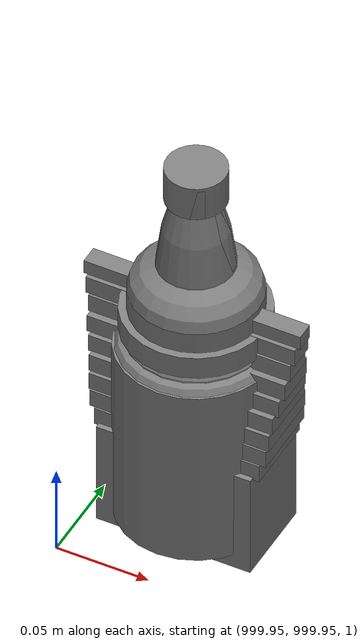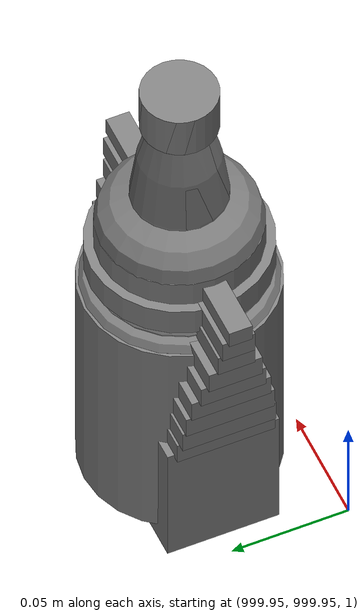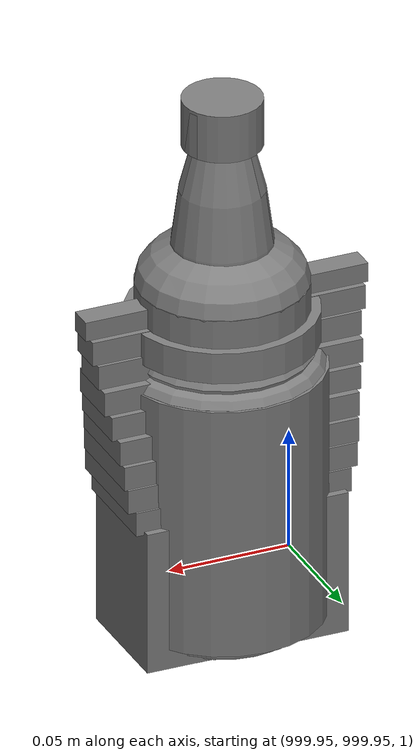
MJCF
<mujoco>
    <option gravity="0.000000000 0.000000000 -9.810000420" timestep="0.0166666" integrator="implicitfast" density="1.225" viscosity="1.8000001e-05" noslip_iterations="10" iterations="100" sdf_iterations="50">
        <flag multiccd="disable"/>
    </option>
    <size memory="1000M"/>
    <compiler coordinate="local"/>
    <worldbody>
        <light cutoff="30" pos="0 1 1" dir="0 -1 -2"/>
        <light cutoff="30" pos="0 -1 1" dir="0 1 -2"/>
        <body pos="0.000000000 0.000000000 0.000000000" euler="0.000000000 0.000000000 0.000000000" name=" Static Objects_ Static Objects">
            <geom contype="1" conaffinity="1" density="1000" type="box" material="" rgba="0.500000000 0.500000000 0.500000000 1.000000000" solimp="0.899999976 0.949999988 0.001000000" friction="1.000000000 0.005000000 0.000100000" solref="0.020000000 1.000000000" margin="0" condim="3" group="0" pos="-3.101639986 6.150595188 1.018643856" quat="1.000000000 0.000000000 0.000000000 0.000000000" size="0.050000001 0.579999983 1.019999981" name=" Static Objects_geom_CA90BEE0_549E_473E_BC05_E58743E69001"/>
            <geom contype="1" conaffinity="1" density="1000" type="box" material="" rgba="0.500000000 0.500000000 0.500000000 1.000000000" solimp="0.899999976 0.949999988 0.001000000" friction="1.000000000 0.005000000 0.000100000" solref="0.020000000 1.000000000" margin="0" condim="3" group="0" pos="-2.825197220 6.153595448 1.115278244" quat="0.707107067 0.000000000 0.000000000 0.707106471" size="0.550000012 0.239999995 0.025000000" name=" Static Objects_geom_17D6B573_908B_4199_8964_8AC44BA00D3D"/>
            <geom contype="1" conaffinity="1" density="1000" type="box" material="" rgba="0.500000000 0.500000000 0.500000000 1.000000000" solimp="0.899999976 0.949999988 0.001000000" friction="1.000000000 0.005000000 0.000100000" solref="0.020000000 1.000000000" margin="0" condim="3" group="0" pos="-2.825197220 6.153595448 0.097434282" quat="0.707107067 0.000000000 0.000000000 0.707106471" size="0.550000012 0.239999995 0.098999999" name=" Static Objects_geom_24FA4286_7AE4_4665_BCEF_DBA2F4B80485"/>
            <geom contype="1" conaffinity="1" density="1000" type="box" material="" rgba="0.500000000 0.500000000 0.500000000 1.000000000" solimp="0.899999976 0.949999988 0.001000000" friction="1.000000000 0.005000000 0.000100000" solref="0.020000000 1.000000000" margin="0" condim="3" group="0" pos="-6.293097973 6.153595448 1.114443064" quat="0.707107067 0.000000000 0.000000000 0.707106471" size="0.529999971 3.134999990 0.025000000" name=" Static Objects_geom_4D37AB7A_E86D_4F8F_8F81_075B9368B270"/>
            <geom contype="1" conaffinity="1" density="1000" type="box" material="" rgba="0.500000000 0.500000000 0.500000000 1.000000000" solimp="0.899999976 0.949999988 0.001000000" friction="1.000000000 0.005000000 0.000100000" solref="0.020000000 1.000000000" margin="0" condim="3" group="0" pos="-6.286010742 6.153595448 0.096129179" quat="0.707107067 0.000000000 0.000000000 0.707106471" size="0.529999971 3.134999990 0.098999999" name=" Static Objects_geom_2F787F16_272C_4624_B383_E872BE59AABD"/>
            <geom contype="1" conaffinity="1" density="1000" type="box" material="" rgba="0.500000000 0.500000000 0.500000000 1.000000000" solimp="0.899999976 0.949999988 0.001000000" friction="1.000000000 0.005000000 0.000100000" solref="0.020000000 1.000000000" margin="0" condim="3" group="0" pos="-2.825197220 6.153595448 1.563861728" quat="0.707107067 0.000000000 0.000000000 0.707106471" size="0.550000012 0.239999995 0.025000000" name=" Static Objects_geom_FFE587F9_9263_4FBD_AE8F_376C2D277542"/>
            <geom contype="1" conaffinity="1" density="1000" type="box" material="" rgba="0.500000000 0.500000000 0.500000000 1.000000000" solimp="0.899999976 0.949999988 0.001000000" friction="1.000000000 0.005000000 0.000100000" solref="0.020000000 1.000000000" margin="0" condim="3" group="0" pos="-6.311686516 6.153595448 1.018643856" quat="0.707107067 0.000000000 0.000000000 0.707106471" size="0.050000001 3.150000095 1.019999981" name=" Static Objects_geom_BBA0AC13_FE64_4D4A_AB63_510E741E329E"/>
            <geom contype="1" conaffinity="1" density="1000" type="box" material="" rgba="0.500000000 0.500000000 0.500000000 1.000000000" solimp="0.899999976 0.949999988 0.001000000" friction="1.000000000 0.005000000 0.000100000" solref="0.020000000 1.000000000" margin="0" condim="3" group="0" pos="-2.825197220 6.153595448 0.629031777" quat="0.707107067 0.000000000 0.000000000 0.707106471" size="0.550000012 0.239999995 0.025000000" name=" Static Objects_geom_2C2BABEE_CBB7_44A7_B28D_0B7371E6052F"/>
            <geom contype="1" conaffinity="1" density="1000" type="box" material="" rgba="0.500000000 0.500000000 0.500000000 1.000000000" solimp="0.899999976 0.949999988 0.001000000" friction="1.000000000 0.005000000 0.000100000" solref="0.020000000 1.000000000" margin="0" condim="3" group="0" pos="-6.286010742 6.153595448 1.563861728" quat="0.707107067 0.000000000 0.000000000 0.707106471" size="0.529999971 3.134999990 0.025000000" name=" Static Objects_geom_C29A44D5_0464_4AC9_B7B3_B6048AE56BFE"/>
            <geom contype="1" conaffinity="1" density="1000" type="box" material="" rgba="0.500000000 0.500000000 0.500000000 1.000000000" solimp="0.899999976 0.949999988 0.001000000" friction="1.000000000 0.005000000 0.000100000" solref="0.020000000 1.000000000" margin="0" condim="3" group="0" pos="-6.286010742 6.153595448 0.629031777" quat="0.707107067 0.000000000 0.000000000 0.707106471" size="0.529999971 3.134999990 0.025000000" name=" Static Objects_geom_6C31C949_0D89_41AC_B677_A0510B913FD8"/>
            <geom contype="1" conaffinity="1" density="1000" type="box" material="" rgba="0.500000000 0.500000000 0.500000000 1.000000000" solimp="0.899999976 0.949999988 0.001000000" friction="1.000000000 0.005000000 0.000100000" solref="0.020000000 1.000000000" margin="0" condim="3" group="0" pos="-7.719123363 2.867671013 1.173410416" quat="1.000000000 0.000000000 0.000000000 0.000000000" size="0.250000000 0.250000000 0.079999998" name=" Static Objects_geom_97DC7132_0D0B_4148_8241_BA10274924FB"/>
            <geom contype="1" conaffinity="1" density="1000" type="box" material="" rgba="0.500000000 0.500000000 0.500000000 1.000000000" solimp="0.899999976 0.949999988 0.001000000" friction="1.000000000 0.005000000 0.000100000" solref="0.020000000 1.000000000" margin="0" condim="3" group="0" pos="-7.408766270 3.088089943 1.776644945" quat="0.928051054 0.000000000 0.000000000 0.372453064" size="0.050000001 0.100000001 0.050000001" name=" Static Objects_geom_234E6A5C_1D20_4A52_856F_65349BC6C5F3"/>
            <geom contype="1" conaffinity="1" density="1000" type="box" material="" rgba="0.500000000 0.500000000 0.500000000 1.000000000" solimp="0.899999976 0.949999988 0.001000000" friction="1.000000000 0.005000000 0.000100000" solref="0.020000000 1.000000000" margin="0" condim="3" group="0" pos="-7.719123363 2.958004713 1.530241251" quat="1.000000000 0.000000000 0.000000000 0.000000000" size="0.250000000 0.159999996 0.280000001" name=" Static Objects_geom_0D922AC3_BA73_4757_9058_629EA93E2640"/>
            <geom contype="1" conaffinity="1" density="1000" type="cylinder" material="" rgba="0.500000000 0.500000000 0.500000000 1.000000000" solimp="0.899999976 0.949999988 0.001000000" friction="1.000000000 0.005000000 0.000100000" solref="0.020000000 1.000000000" margin="0" condim="3" group="0" pos="-7.427312374 3.069516420 1.502544641" quat="0.928051054 0.000000000 0.000000000 0.372453064" size="0.015000000 0.230000004 0.100000001" name=" Static Objects_geom_9D708DFF_76FC_442F_BF56_6502480649DC"/>
            <geom contype="1" conaffinity="1" density="1000" type="box" material="" rgba="0.500000000 0.500000000 0.500000000 1.000000000" solimp="0.899999976 0.949999988 0.001000000" friction="1.000000000 0.005000000 0.000100000" solref="0.020000000 1.000000000" margin="0" condim="3" group="0" pos="-7.437745571 3.067511320 1.289965630" quat="1.000000000 0.000000000 0.000000000 0.000000000" size="0.029999999 0.020000000 0.020000000" name=" Static Objects_geom_F254D5C9_9C80_452B_BFFD_5AF002040717"/>
            <geom contype="1" conaffinity="1" density="1000" type="box" material="" rgba="0.500000000 0.500000000 0.500000000 1.000000000" solimp="0.899999976 0.949999988 0.001000000" friction="1.000000000 0.005000000 0.000100000" solref="0.020000000 1.000000000" margin="0" condim="3" group="0" pos="-9.058088303 6.434794426 1.209077358" quat="1.000000000 0.000000000 0.000000000 0.000000000" size="0.250000000 0.100000001 0.070000000" name=" Static Objects_geom_CDA0B892_89CC_43BC_9850_E0B4AF21D025"/>
            <geom contype="1" conaffinity="1" density="1000" type="box" material="" rgba="0.500000000 0.500000000 0.500000000 1.000000000" solimp="0.899999976 0.949999988 0.001000000" friction="1.000000000 0.005000000 0.000100000" solref="0.020000000 1.000000000" margin="0" condim="3" group="0" pos="-7.886891365 6.459744930 0.352518857" quat="1.000000000 0.000000000 0.000000000 0.000000000" size="1.500000000 0.200000003 0.150000006" name=" Static Objects_geom_864D4FF5_0C48_4E40_8372_B2077BDF0294"/>
            <geom contype="1" conaffinity="1" density="1000" type="box" material="" rgba="0.500000000 0.500000000 0.500000000 1.000000000" solimp="0.899999976 0.949999988 0.001000000" friction="1.000000000 0.005000000 0.000100000" solref="0.020000000 1.000000000" margin="0" condim="3" group="0" pos="-9.237723351 6.464855671 1.209077358" quat="1.000000000 0.000000000 0.000000000 0.000000000" size="0.100000001 0.100000001 0.070000000" name=" Static Objects_geom_98832257_63B9_4FE7_BD25_F4B141E2E768"/>
            <geom contype="1" conaffinity="1" density="1000" type="box" material="" rgba="0.500000000 0.500000000 0.500000000 1.000000000" solimp="0.899999976 0.949999988 0.001000000" friction="1.000000000 0.005000000 0.000100000" solref="0.020000000 1.000000000" margin="0" condim="3" group="0" pos="-6.924745083 6.362090111 1.214329123" quat="1.000000000 0.000000000 0.000000000 0.000000000" size="0.200000003 0.100000001 0.075000003" name=" Static Objects_geom_9B37CB51_5B15_49EB_B03B_C593ADA54780"/>
            <geom contype="1" conaffinity="1" density="1000" type="box" material="" rgba="0.500000000 0.500000000 0.500000000 1.000000000" solimp="0.899999976 0.949999988 0.001000000" friction="1.000000000 0.005000000 0.000100000" solref="0.020000000 1.000000000" margin="0" condim="3" group="0" pos="-4.407354832 6.459744930 1.292199373" quat="1.000000000 0.000000000 0.000000000 0.000000000" size="1.240000010 0.200000003 0.150000006" name=" Static Objects_geom_2752CDC6_2F54_4FCE_9F7F_FEBE844F3881"/>
            <geom contype="1" conaffinity="1" density="1000" type="box" material="" rgba="0.500000000 0.500000000 0.500000000 1.000000000" solimp="0.899999976 0.949999988 0.001000000" friction="1.000000000 0.005000000 0.000100000" solref="0.020000000 1.000000000" margin="0" condim="3" group="0" pos="-5.611940861 6.318420410 0.350975692" quat="1.000000000 0.000000000 0.000000000 0.000000000" size="0.699999988 0.100000001 0.150000006" name=" Static Objects_geom_9A6002E7_73E4_4D4D_8AF3_63D264DF053F"/>
            <geom contype="1" conaffinity="1" density="1000" type="box" material="" rgba="0.500000000 0.500000000 0.500000000 1.000000000" solimp="0.899999976 0.949999988 0.001000000" friction="1.000000000 0.005000000 0.000100000" solref="0.020000000 1.000000000" margin="0" condim="3" group="0" pos="-6.300771236 6.459744930 1.744376063" quat="1.000000000 0.000000000 0.000000000 0.000000000" size="3.000000000 0.200000003 0.150000006" name=" Static Objects_geom_B938D3E0_DA97_48EB_BBA7_A8A9B4D68216"/>
            <geom contype="1" conaffinity="1" density="1000" type="box" material="" rgba="0.500000000 0.500000000 0.500000000 1.000000000" solimp="0.899999976 0.949999988 0.001000000" friction="1.000000000 0.005000000 0.000100000" solref="0.020000000 1.000000000" margin="0" condim="3" group="0" pos="-6.751636982 6.459744930 0.800981164" quat="1.000000000 0.000000000 0.000000000 0.000000000" size="2.200000048 0.200000003 0.150000006" name=" Static Objects_geom_7A107990_EC9B_431E_A99E_715AB5A0683A"/>
            <geom contype="1" conaffinity="1" density="1000" type="box" material="" rgba="0.500000000 0.500000000 0.500000000 1.000000000" solimp="0.899999976 0.949999988 0.001000000" friction="1.000000000 0.005000000 0.000100000" solref="0.020000000 1.000000000" margin="0" condim="3" group="0" pos="-8.844120979 6.464855671 1.209077358" quat="1.000000000 0.000000000 0.000000000 0.000000000" size="0.100000001 0.100000001 0.070000000" name=" Static Objects_geom_7B711B3B_B482_483B_BECB_48EC9F8247AF"/>
            <geom contype="1" conaffinity="1" density="1000" type="box" material="" rgba="0.500000000 0.500000000 0.500000000 1.000000000" solimp="0.899999976 0.949999988 0.001000000" friction="1.000000000 0.005000000 0.000100000" solref="0.020000000 1.000000000" margin="0" condim="3" group="0" pos="-6.098561764 6.327973843 1.292199373" quat="1.000000000 0.000000000 0.000000000 0.000000000" size="0.500000000 0.100000001 0.150000006" name=" Static Objects_geom_1EBE4662_EAA1_43A6_91D3_81FA1E00EA58"/>
            <geom contype="1" conaffinity="1" density="1000" type="box" material="" rgba="0.500000000 0.500000000 0.500000000 1.000000000" solimp="0.899999976 0.949999988 0.001000000" friction="1.000000000 0.005000000 0.000100000" solref="0.020000000 1.000000000" margin="0" condim="3" group="0" pos="-6.824534416 6.447464466 1.212718010" quat="1.000000000 0.000000000 0.000000000 0.000000000" size="0.100000001 0.100000001 0.075000003" name=" Static Objects_geom_B762B0F2_09A6_4E61_9C6D_20FFE0C113A5"/>
            <geom contype="1" conaffinity="1" density="1000" type="box" material="" rgba="0.500000000 0.500000000 0.500000000 1.000000000" solimp="0.899999976 0.949999988 0.001000000" friction="1.000000000 0.005000000 0.000100000" solref="0.020000000 1.000000000" margin="0" condim="3" group="0" pos="-3.907610416 6.318625927 0.800981164" quat="1.000000000 0.000000000 0.000000000 0.000000000" size="0.500000000 0.100000001 0.150000006" name=" Static Objects_geom_2BD852EA_1C41_4E67_85C4_FA64D05D37D0"/>
            <geom contype="1" conaffinity="1" density="1000" type="box" material="" rgba="0.500000000 0.500000000 0.500000000 1.000000000" solimp="0.899999976 0.949999988 0.001000000" friction="1.000000000 0.005000000 0.000100000" solref="0.020000000 1.000000000" margin="0" condim="3" group="0" pos="-7.373087406 6.458900928 1.214329123" quat="1.000000000 0.000000000 0.000000000 0.000000000" size="0.250000000 0.200000003 0.075000003" name=" Static Objects_geom_20006AEC_C73E_4CD4_829B_7457558F61FF"/>
            <geom contype="1" conaffinity="1" density="1000" type="box" material="" rgba="0.500000000 0.500000000 0.500000000 1.000000000" solimp="0.899999976 0.949999988 0.001000000" friction="1.000000000 0.005000000 0.000100000" solref="0.020000000 1.000000000" margin="0" condim="3" group="0" pos="-4.035642624 6.459744930 0.352518857" quat="1.000000000 0.000000000 0.000000000 0.000000000" size="0.800000012 0.200000003 0.150000006" name=" Static Objects_geom_D6FD74D0_063C_45CB_B037_FB6812FB035D"/>
            <geom contype="1" conaffinity="1" density="1000" type="box" material="" rgba="0.500000000 0.500000000 0.500000000 1.000000000" solimp="0.899999976 0.949999988 0.001000000" friction="1.000000000 0.005000000 0.000100000" solref="0.020000000 1.000000000" margin="0" condim="3" group="0" pos="-6.460197449 2.937205315 0.548931718" quat="1.000000000 0.000000000 0.000000000 0.000000000" size="2.650000095 0.430000007 0.550000012" name=" Static Objects_geom_BB7EF24A_3549_486D_BD86_E3DC0A645B20"/>
            <geom contype="1" conaffinity="1" density="1000" type="box" material="" rgba="0.500000000 0.500000000 0.500000000 1.000000000" solimp="0.899999976 0.949999988 0.001000000" friction="1.000000000 0.005000000 0.000100000" solref="0.020000000 1.000000000" margin="0" condim="3" group="0" pos="-4.240264893 1.327049494 0.549888909" quat="1.000000000 0.000000000 0.000000000 0.000000000" size="0.430000007 1.200000048 0.550000012" name=" Static Objects_geom_315E99D4_079C_4DBA_A5B5_ED508D0451A8"/>
            <geom contype="1" conaffinity="1" density="1000" type="box" material="" rgba="0.500000000 0.500000000 0.500000000 1.000000000" solimp="0.899999976 0.949999988 0.001000000" friction="1.000000000 0.005000000 0.000100000" solref="0.020000000 1.000000000" margin="0" condim="3" group="0" pos="-8.830721855 2.096410990 0.549305558" quat="1.000000000 0.000000000 0.000000000 0.000000000" size="0.280000001 0.430000007 0.550000012" name=" Static Objects_geom_A85CDCDE_5603_4D84_B554_D30210D8C38B"/>
            <geom contype="1" conaffinity="1" density="1000" type="plane" material="" rgba="0.500000000 0.500000000 0.500000000 1.000000000" solimp="0.899999976 0.949999988 0.001000000" friction="1.000000000 0.005000000 0.000100000" solref="0.020000000 1.000000000" margin="0" condim="3" group="0" pos="-6.000000000 10.399999619 0.000000000" quat="1.000000000 0.000000000 0.000000000 0.000000000" size="6.050000191 10.800000191 0.010000000" name=" Static Objects_geom_7E5A1846_8072_4103_8EBA_1EB4FCE6E319"/>
            <geom contype="1" conaffinity="1" density="1000" type="box" material="" rgba="0.500000000 0.500000000 0.500000000 1.000000000" solimp="0.899999976 0.949999988 0.001000000" friction="1.000000000 0.005000000 0.000100000" solref="0.020000000 1.000000000" margin="0" condim="3" group="0" pos="-6.000000000 0.035000000 2.000000000" quat="1.000000000 0.000000000 0.000000000 0.000000000" size="6.079999924 0.070000000 2.000000000" name=" Static Objects_geom_CB0836B3_DC93_478F_9116_C5D32D3A5863"/>
            <geom contype="1" conaffinity="1" density="1000" type="box" material="" rgba="0.500000000 0.500000000 0.500000000 1.000000000" solimp="0.899999976 0.949999988 0.001000000" friction="1.000000000 0.005000000 0.000100000" solref="0.020000000 1.000000000" margin="0" condim="3" group="0" pos="-6.000000000 20.159999847 2.000000000" quat="1.000000000 0.000000000 0.000000000 0.000000000" size="6.079999924 0.070000000 2.000000000" name=" Static Objects_geom_555B4B69_FC19_4284_9AF9_270BF5867B0C"/>
            <geom contype="1" conaffinity="1" density="1000" type="box" material="" rgba="0.500000000 0.500000000 0.500000000 1.000000000" solimp="0.899999976 0.949999988 0.001000000" friction="1.000000000 0.005000000 0.000100000" solref="0.020000000 1.000000000" margin="0" condim="3" group="0" pos="0.000000000 10.000000000 2.000000000" quat="1.000000000 0.000000000 0.000000000 0.000000000" size="0.070000000 10.500000000 2.000000000" name=" Static Objects_geom_C4D04430_2885_423D_A982_A079284B61EC"/>
            <geom contype="1" conaffinity="1" density="1000" type="box" material="" rgba="0.500000000 0.500000000 0.500000000 1.000000000" solimp="0.899999976 0.949999988 0.001000000" friction="1.000000000 0.005000000 0.000100000" solref="0.020000000 1.000000000" margin="0" condim="3" group="0" pos="-12.050000191 10.000000000 2.000000000" quat="1.000000000 0.000000000 0.000000000 0.000000000" size="0.070000000 10.500000000 2.000000000" name=" Static Objects_geom_2A16C9CE_B0DB_436F_8F70_611A6EBC1A6F"/>
        </body>
        <body pos="-2.067876816 6.400743961 1.737085581" euler="-107.775451660 -75.903686523 65.380577087" mocap="true" name="spotlight5_SpotLight"/>
        <body pos="1000.000000000 1000.000000000 1.000000000" euler="0.000000000 0.000000000 0.000000000" name="openloong_gripper_2f85_fix_base_usda_jar_01">
            <geom contype="1" conaffinity="1" density="1000" type="box" material="" rgba="0.500000000 0.500000000 0.500000000 1.000000000" solimp="0.899999976 0.949999988 0.001000000" friction="1.000000000 0.005000000 0.000100000" solref="0.020000000 1.000000000" margin="0" condim="3" group="0" pos="0.000000000 0.000000000 0.006158113" quat="1.000000000 0.000000000 0.000000000 0.000000000" size="0.020000000 0.020000000 0.005000000" name="openloong_gripper_2f85_fix_base_usda_geom_D607EAA7_1F21_41CF_80D6_9E4C6CDEDF46"/>
            <geom contype="1" conaffinity="1" density="1000" type="cylinder" material="" rgba="0.500000000 0.500000000 0.500000000 1.000000000" solimp="0.899999976 0.949999988 0.001000000" friction="1.000000000 0.005000000 0.000100000" solref="0.020000000 1.000000000" margin="0" condim="3" group="0" pos="0.000000000 0.000000000 0.062744498" quat="1.000000000 0.000000000 0.000000000 0.000000000" size="0.041000001 0.052999999 1.000000000" name="openloong_gripper_2f85_fix_base_usda_geom_E9A7EB66_C623_4BD1_9E1A_F2F35BA42515"/>
            <geom contype="1" conaffinity="1" density="1000" type="ellipsoid" material="" rgba="0.500000000 0.500000000 0.500000000 1.000000000" solimp="0.899999976 0.949999988 0.001000000" friction="1.000000000 0.005000000 0.000100000" solref="0.020000000 1.000000000" margin="0" condim="3" group="0" pos="0.000000000 0.000000000 0.122252703" quat="1.000000000 0.000000000 0.000000000 0.000000000" size="0.035999998 0.035999998 0.010000000" name="openloong_gripper_2f85_fix_base_usda_geom_B7F50CA2_70C5_49A2_90C3_EAF8EE878818"/>
            <geom contype="1" conaffinity="1" density="1000" type="cylinder" material="" rgba="0.500000000 0.500000000 0.500000000 1.000000000" solimp="0.899999976 0.949999988 0.001000000" friction="1.000000000 0.005000000 0.000100000" solref="0.020000000 1.000000000" margin="0" condim="3" group="0" pos="0.000000000 0.000000000 0.015747190" quat="1.000000000 0.000000000 0.000000000 0.000000000" size="0.035000000 0.010000000 1.000000000" name="openloong_gripper_2f85_fix_base_usda_geom_1DA28CAE_C5D1_4379_AC00_20CB7B0E27D1"/>
            <geom contype="1" conaffinity="1" density="1000" type="ellipsoid" material="" rgba="0.500000000 0.500000000 0.500000000 1.000000000" solimp="0.899999976 0.949999988 0.001000000" friction="1.000000000 0.005000000 0.000100000" solref="0.020000000 1.000000000" margin="0" condim="3" group="0" pos="0.000000000 0.000000000 0.115815401" quat="1.000000000 0.000000000 0.000000000 0.000000000" size="0.039999999 0.039999999 0.010000000" name="openloong_gripper_2f85_fix_base_usda_geom_EF03E917_0FC1_4D26_9084_8886646F9497"/>
            <geom contype="1" conaffinity="1" density="1000" type="cylinder" material="" rgba="0.500000000 0.500000000 0.500000000 1.000000000" solimp="0.899999976 0.949999988 0.001000000" friction="1.000000000 0.005000000 0.000100000" solref="0.020000000 1.000000000" margin="0" condim="3" group="0" pos="0.000000000 0.000000000 0.133183479" quat="1.000000000 0.000000000 0.000000000 0.000000000" size="0.037999999 0.006500000 1.000000000" name="openloong_gripper_2f85_fix_base_usda_geom_DE27616D_7291_4AA3_9EAE_9979E72CE138"/>
            <freejoint name="openloong_gripper_2f85_fix_base_usda_jar_01_joint"/>
            <site size="0.005000000 0.005000000 0.005000000" rgba="0.500000000 0.500000000 0.500000000 1.000000000" pos="0.000000000 0.000000000 0.000000000" quat="1.000000000 0.000000000 0.000000000 0.000000000" group="0" type="sphere" name="openloong_gripper_2f85_fix_base_usda_jar_01site"/>
        </body>
        <body pos="-1.948114276 6.034964085 1.671361685" euler="-170.748153687 -26.249530792 -126.040382385" mocap="true" name="spotlight6_SpotLight"/>
        <body pos="1000.000000000 1000.000000000 1.000000000" euler="0.000000000 0.000000000 0.000000000" name="openloong_gripper_2f85_fix_base_usda_bottle_blue">
            <geom contype="1" conaffinity="1" density="1000" type="ellipsoid" material="" rgba="0.500000000 0.500000000 0.500000000 1.000000000" solimp="0.899999976 0.949999988 0.001000000" friction="1.000000000 0.005000000 0.000100000" solref="0.020000000 1.000000000" margin="0" condim="3" group="0" pos="0.000000000 0.000000000 0.118920922" quat="1.000000000 0.000000000 0.000000000 0.000000000" size="0.030999999 0.030999999 0.029999999" name="openloong_gripper_2f85_fix_base_usda_geom_4740E463_0524_4392_ABB3_A3D43F77AF60"/>
            <geom contype="1" conaffinity="1" density="1000" type="box" material="" rgba="0.500000000 0.500000000 0.500000000 1.000000000" solimp="0.899999976 0.949999988 0.001000000" friction="1.000000000 0.005000000 0.000100000" solref="0.020000000 1.000000000" margin="0" condim="3" group="0" pos="0.000000000 0.000000000 0.002164602" quat="1.000000000 0.000000000 0.000000000 0.000000000" size="0.020000000 0.020000000 0.003000000" name="openloong_gripper_2f85_fix_base_usda_geom_D1166A2D_A24E_4008_81DC_CEADDC269C9A"/>
            <geom contype="1" conaffinity="1" density="1000" type="cylinder" material="" rgba="0.500000000 0.500000000 0.500000000 1.000000000" solimp="0.899999976 0.949999988 0.001000000" friction="1.000000000 0.005000000 0.000100000" solref="0.020000000 1.000000000" margin="0" condim="3" group="0" pos="0.000000000 -0.000366211 0.060859680" quat="1.000000000 0.000000000 0.000000000 0.000000000" size="0.030999999 0.057999998 1.000000000" name="openloong_gripper_2f85_fix_base_usda_geom_02BBA997_8821_4364_8C40_203F43A1DE5F"/>
            <geom contype="1" conaffinity="1" density="1000" type="cylinder" material="" rgba="0.500000000 0.500000000 0.500000000 1.000000000" solimp="0.899999976 0.949999988 0.001000000" friction="1.000000000 0.005000000 0.000100000" solref="0.020000000 1.000000000" margin="0" condim="3" group="0" pos="0.000000000 0.000000000 0.220594406" quat="1.000000000 0.000000000 0.000000000 0.000000000" size="0.016000001 0.010000000 1.000000000" name="openloong_gripper_2f85_fix_base_usda_geom_D02A7FF7_4A01_44AD_8F77_D12A43A9F3D7"/>
            <geom contype="1" conaffinity="1" density="1000" type="ellipsoid" material="" rgba="0.500000000 0.500000000 0.500000000 1.000000000" solimp="0.899999976 0.949999988 0.001000000" friction="1.000000000 0.005000000 0.000100000" solref="0.020000000 1.000000000" margin="0" condim="3" group="0" pos="0.000000000 0.000000000 0.144259930" quat="1.000000000 0.000000000 0.000000000 0.000000000" size="0.021000000 0.021000000 0.079999998" name="openloong_gripper_2f85_fix_base_usda_geom_E34F9CA4_AF48_4F86_8D76_17C27AF705E2"/>
            <freejoint name="openloong_gripper_2f85_fix_base_usda_bottle_blue_joint"/>
            <site size="0.005000000 0.005000000 0.005000000" rgba="0.500000000 0.500000000 0.500000000 1.000000000" pos="0.000000000 0.000000000 0.000000000" quat="0.999961913 0.008726535 0.000000000 0.000000000" group="0" type="sphere" name="openloong_gripper_2f85_fix_base_usda_bottle_bluesite"/>
        </body>
        <body pos="-2.352505445 6.378284931 1.824421167" euler="-100.425407410 61.313663483 -119.443801880" mocap="true" name="spotlight3_SpotLight"/>
        <body pos="1000.000000000 1000.000000000 1.000000000" euler="0.000000000 0.000000000 0.000000000" name="openloong_gripper_2f85_fix_base_usda_salt">
            <geom contype="1" conaffinity="1" density="1000" type="box" material="" rgba="0.500000000 0.500000000 0.500000000 1.000000000" solimp="0.899999976 0.949999988 0.001000000" friction="1.000000000 0.005000000 0.000100000" solref="0.020000000 1.000000000" margin="0" condim="3" group="0" pos="0.000305176 0.000000000 0.084862232" quat="1.000000000 0.000000000 0.000000000 0.000000000" size="0.048999999 0.018999999 0.005000000" name="openloong_gripper_2f85_fix_base_usda_geom_2FF7DEE6_ACF6_4A07_A82E_ABC438C83448"/>
            <geom contype="1" conaffinity="1" density="1000" type="box" material="" rgba="0.500000000 0.500000000 0.500000000 1.000000000" solimp="0.899999976 0.949999988 0.001000000" friction="1.000000000 0.005000000 0.000100000" solref="0.020000000 1.000000000" margin="0" condim="3" group="0" pos="0.000305176 0.000000000 0.104564309" quat="1.000000000 0.000000000 0.000000000 0.000000000" size="0.052000001 0.014000000 0.005000000" name="openloong_gripper_2f85_fix_base_usda_geom_9E4B8D42_80CD_4302_BDD2_568D5513F11F"/>
            <geom contype="1" conaffinity="1" density="1000" type="box" material="" rgba="0.500000000 0.500000000 0.500000000 1.000000000" solimp="0.899999976 0.949999988 0.001000000" friction="1.000000000 0.005000000 0.000100000" solref="0.020000000 1.000000000" margin="0" condim="3" group="0" pos="0.000305176 0.000000000 0.114487171" quat="1.000000000 0.000000000 0.000000000 0.000000000" size="0.054000001 0.011500000 0.005000000" name="openloong_gripper_2f85_fix_base_usda_geom_AE539FBD_EB8B_49AF_B93D_22B028559375"/>
            <geom contype="1" conaffinity="1" density="1000" type="box" material="" rgba="0.500000000 0.500000000 0.500000000 1.000000000" solimp="0.899999976 0.949999988 0.001000000" friction="1.000000000 0.005000000 0.000100000" solref="0.020000000 1.000000000" margin="0" condim="3" group="0" pos="0.000305176 0.000000000 0.075103164" quat="1.000000000 0.000000000 0.000000000 0.000000000" size="0.048000000 0.020000000 0.005000000" name="openloong_gripper_2f85_fix_base_usda_geom_5F83BD61_0230_4CCB_B231_215D17E50204"/>
            <geom contype="1" conaffinity="1" density="1000" type="box" material="" rgba="0.500000000 0.500000000 0.500000000 1.000000000" solimp="0.899999976 0.949999988 0.001000000" friction="1.000000000 0.005000000 0.000100000" solref="0.020000000 1.000000000" margin="0" condim="3" group="0" pos="0.000305176 0.000000000 0.134892464" quat="1.000000000 0.000000000 0.000000000 0.000000000" size="0.057000000 0.007000000 0.005000000" name="openloong_gripper_2f85_fix_base_usda_geom_839D9E51_4DAD_4484_8DDD_288C15CBC1AC"/>
            <geom contype="1" conaffinity="1" density="1000" type="box" material="" rgba="0.500000000 0.500000000 0.500000000 1.000000000" solimp="0.899999976 0.949999988 0.001000000" friction="1.000000000 0.005000000 0.000100000" solref="0.020000000 1.000000000" margin="0" condim="3" group="0" pos="0.000305176 0.000000000 0.094920278" quat="1.000000000 0.000000000 0.000000000 0.000000000" size="0.050000001 0.017000001 0.005000000" name="openloong_gripper_2f85_fix_base_usda_geom_FFB89F15_2AF7_4E71_AD02_7438443001F3"/>
            <geom contype="1" conaffinity="1" density="1000" type="box" material="" rgba="0.500000000 0.500000000 0.500000000 1.000000000" solimp="0.899999976 0.949999988 0.001000000" friction="1.000000000 0.005000000 0.000100000" solref="0.020000000 1.000000000" margin="0" condim="3" group="0" pos="0.000305176 0.000000000 0.065204859" quat="1.000000000 0.000000000 0.000000000 0.000000000" size="0.045000002 0.021000000 0.005000000" name="openloong_gripper_2f85_fix_base_usda_geom_70F200C2_B2E9_404F_96A2_D5ABBF563261"/>
            <geom contype="1" conaffinity="1" density="1000" type="box" material="" rgba="0.500000000 0.500000000 0.500000000 1.000000000" solimp="0.899999976 0.949999988 0.001000000" friction="1.000000000 0.005000000 0.000100000" solref="0.020000000 1.000000000" margin="0" condim="3" group="0" pos="0.000305176 0.000000000 0.144135714" quat="1.000000000 0.000000000 0.000000000 0.000000000" size="0.059000000 0.005000000 0.004000000" name="openloong_gripper_2f85_fix_base_usda_geom_45154159_3F69_466A_B827_683748268209"/>
            <geom contype="1" conaffinity="1" density="1000" type="box" material="" rgba="0.500000000 0.500000000 0.500000000 1.000000000" solimp="0.899999976 0.949999988 0.001000000" friction="1.000000000 0.005000000 0.000100000" solref="0.020000000 1.000000000" margin="0" condim="3" group="0" pos="0.000000000 0.000000000 0.031593561" quat="1.000000000 0.000000000 0.000000000 0.000000000" size="0.041999999 0.024000000 0.029999999" name="openloong_gripper_2f85_fix_base_usda_geom_149326E2_BCFA_4638_919A_627CA77DA1C3"/>
            <geom contype="1" conaffinity="1" density="1000" type="box" material="" rgba="0.500000000 0.500000000 0.500000000 1.000000000" solimp="0.899999976 0.949999988 0.001000000" friction="1.000000000 0.005000000 0.000100000" solref="0.020000000 1.000000000" margin="0" condim="3" group="0" pos="0.000305176 0.000000000 0.124608755" quat="1.000000000 0.000000000 0.000000000 0.000000000" size="0.055000000 0.008000000 0.005000000" name="openloong_gripper_2f85_fix_base_usda_geom_7318F7C0_9D44_458E_BB17_7FB86C614722"/>
            <freejoint name="openloong_gripper_2f85_fix_base_usda_salt_joint"/>
            <site size="0.005000000 0.005000000 0.005000000" rgba="0.500000000 0.500000000 0.500000000 1.000000000" pos="0.000000000 0.000000000 0.000000000" quat="1.000000000 0.000000000 0.000000000 0.000000000" group="0" type="sphere" name="openloong_gripper_2f85_fix_base_usda_saltsite"/>
        </body>
        <body pos="1000.000000000 1000.000000000 1.000000000" euler="0.000000000 0.000000000 0.000000000" name="openloong_gripper_2f85_fix_base_usda_bottle_red">
            <geom contype="1" conaffinity="1" density="1000" type="ellipsoid" material="" rgba="0.500000000 0.500000000 0.500000000 1.000000000" solimp="0.899999976 0.949999988 0.001000000" friction="1.000000000 0.005000000 0.000100000" solref="0.020000000 1.000000000" margin="0" condim="3" group="0" pos="0.000000000 0.000000000 0.144284487" quat="1.000000000 0.000000000 0.000000000 0.000000000" size="0.021000000 0.021000000 0.079999998" name="openloong_gripper_2f85_fix_base_usda_geom_E2360AC4_2A1C_4AB9_9115_AF45FF9085D9"/>
            <geom contype="1" conaffinity="1" density="1000" type="cylinder" material="" rgba="0.500000000 0.500000000 0.500000000 1.000000000" solimp="0.899999976 0.949999988 0.001000000" friction="1.000000000 0.005000000 0.000100000" solref="0.020000000 1.000000000" margin="0" condim="3" group="0" pos="0.000000000 0.000000000 0.220618963" quat="1.000000000 0.000000000 0.000000000 0.000000000" size="0.016000001 0.010000000 1.000000000" name="openloong_gripper_2f85_fix_base_usda_geom_14B50C5B_CE3B_405E_83D6_918591D5785A"/>
            <geom contype="1" conaffinity="1" density="1000" type="ellipsoid" material="" rgba="0.500000000 0.500000000 0.500000000 1.000000000" solimp="0.899999976 0.949999988 0.001000000" friction="1.000000000 0.005000000 0.000100000" solref="0.020000000 1.000000000" margin="0" condim="3" group="0" pos="0.000000000 0.000000000 0.118945479" quat="1.000000000 0.000000000 0.000000000 0.000000000" size="0.030999999 0.030999999 0.029999999" name="openloong_gripper_2f85_fix_base_usda_geom_7E901F46_8137_4896_AFFE_AE327FEB9967"/>
            <geom contype="1" conaffinity="1" density="1000" type="box" material="" rgba="0.500000000 0.500000000 0.500000000 1.000000000" solimp="0.899999976 0.949999988 0.001000000" friction="1.000000000 0.005000000 0.000100000" solref="0.020000000 1.000000000" margin="0" condim="3" group="0" pos="0.000000000 0.000000000 0.002189159" quat="1.000000000 0.000000000 0.000000000 0.000000000" size="0.020000000 0.020000000 0.003000000" name="openloong_gripper_2f85_fix_base_usda_geom_75C6C2CE_71EC_46F1_8F51_7222349E9A09"/>
            <geom contype="1" conaffinity="1" density="1000" type="cylinder" material="" rgba="0.500000000 0.500000000 0.500000000 1.000000000" solimp="0.899999976 0.949999988 0.001000000" friction="1.000000000 0.005000000 0.000100000" solref="0.020000000 1.000000000" margin="0" condim="3" group="0" pos="0.000000000 -0.000366211 0.060884237" quat="1.000000000 0.000000000 0.000000000 0.000000000" size="0.030999999 0.057999998 1.000000000" name="openloong_gripper_2f85_fix_base_usda_geom_9BBD901D_8E2F_4C11_8A94_FABAE51C29B6"/>
            <freejoint name="openloong_gripper_2f85_fix_base_usda_bottle_red_joint"/>
            <site size="0.005000000 0.005000000 0.005000000" rgba="0.500000000 0.500000000 0.500000000 1.000000000" pos="0.000000000 0.000000000 0.000000000" quat="0.999961913 0.008726535 0.000000000 0.000000000" group="0" type="sphere" name="openloong_gripper_2f85_fix_base_usda_bottle_redsite"/>
        </body>
        <body pos="1000.000000000 1000.000000000 1.000000000" euler="0.000000000 0.000000000 0.000000000" name="openloong_gripper_2f85_fix_base_usda_can">
            <geom contype="1" conaffinity="1" density="1000" type="cylinder" material="" rgba="0.500000000 0.500000000 0.500000000 1.000000000" solimp="0.899999976 0.949999988 0.001000000" friction="1.000000000 0.005000000 0.000100000" solref="0.020000000 1.000000000" margin="0" condim="3" group="0" pos="0.000000000 0.000000000 0.079676986" quat="1.000000000 0.000000000 0.000000000 0.000000000" size="0.034000002 0.071999997 1.000000000" name="openloong_gripper_2f85_fix_base_usda_geom_4B18E4AC_5024_4CCB_B46B_C3F7C091572E"/>
            <geom contype="1" conaffinity="1" density="1000" type="ellipsoid" material="" rgba="0.500000000 0.500000000 0.500000000 1.000000000" solimp="0.899999976 0.949999988 0.001000000" friction="1.000000000 0.005000000 0.000100000" solref="0.020000000 1.000000000" margin="0" condim="3" group="0" pos="0.000000000 0.000000000 0.151854277" quat="1.000000000 0.000000000 0.000000000 0.000000000" size="0.034000002 0.034000002 0.020000000" name="openloong_gripper_2f85_fix_base_usda_geom_AD4D2905_118D_424D_B552_835A060AAE6D"/>
            <geom contype="1" conaffinity="1" density="1000" type="box" material="" rgba="0.500000000 0.500000000 0.500000000 1.000000000" solimp="0.899999976 0.949999988 0.001000000" friction="1.000000000 0.005000000 0.000100000" solref="0.020000000 1.000000000" margin="0" condim="3" group="0" pos="0.000000000 0.000000000 0.004777670" quat="1.000000000 0.000000000 0.000000000 0.000000000" size="0.020000000 0.020000000 0.005000000" name="openloong_gripper_2f85_fix_base_usda_geom_4DA6F3CB_D718_4D63_8C78_8A2CCD55CDD3"/>
            <freejoint name="openloong_gripper_2f85_fix_base_usda_can_joint"/>
            <site size="0.005000000 0.005000000 0.005000000" rgba="0.500000000 0.500000000 0.500000000 1.000000000" pos="0.000000000 0.000000000 0.000000000" quat="1.000000000 0.000000000 0.000000000 0.000000000" group="0" type="sphere" name="openloong_gripper_2f85_fix_base_usda_cansite"/>
        </body>
        <body pos="0.000000000 0.000000000 0.000000000" euler="0.000000000 0.000000000 0.000000000" name="Interactive Objects_Interactive Objects"/>
        <body pos="-3.510578632 3.403555870 -0.000000100" euler="0.000000000 0.000000000 40.200675964" name="openloong_gripper_2f85_fix_base_usda_PZ">
            <geom contype="1" conaffinity="1" density="1000" type="box" material="" rgba="0.500000000 0.500000000 0.500000000 1.000000000" solimp="0.899999976 0.949999988 0.001000000" friction="1.000000000 0.005000000 0.000100000" solref="0.020000000 1.000000000" margin="0" condim="3" group="0" pos="-0.047453165 0.056484699 0.373715430" quat="0.934750080 0.077914521 0.028795123 0.345459938" size="0.180000007 0.010000000 0.379999995" name="openloong_gripper_2f85_fix_base_usda_geom_7783D871_C7E2_4E23_B44F_444B8DB4672B"/>
            <geom contype="1" conaffinity="1" density="1000" type="box" material="" rgba="0.500000000 0.500000000 0.500000000 1.000000000" solimp="0.899999976 0.949999988 0.001000000" friction="1.000000000 0.005000000 0.000100000" solref="0.020000000 1.000000000" margin="0" condim="3" group="0" pos="0.047452450 -0.054376602 0.374072611" quat="0.934387863 -0.082143910 -0.030358355 0.345326364" size="0.180000007 0.010000000 0.379999995" name="openloong_gripper_2f85_fix_base_usda_geom_1C5D3CD9_5136_47F4_9D8C_60958459563A"/>
            <freejoint name="openloong_gripper_2f85_fix_base_usda_PZ"/>
        </body>
        <body pos="-6.332345009 2.779978037 1.034067392" euler="0.000000000 0.000000000 0.000000000" name="openloong_gripper_2f85_fix_base_usda_basket">
            <geom contype="1" conaffinity="1" density="100000" type="box" material="" rgba="0.500000000 0.500000000 0.500000000 1.000000000" solimp="0.899999976 0.949999988 0.001000000" friction="1.000000000 0.899999976 0.000100000" solref="0.020000000 1.000000000" margin="0" condim="3" group="0" pos="-0.172339439 0.000000000 0.168361664" quat="0.706172407 -0.036353018 -0.036353093 0.706170976" size="0.200000003 0.006000000 0.108000003" name="openloong_gripper_2f85_fix_base_usda_geom_19F76EBD_B41E_46AB_BAF2_5C5DA49B652D"/>
            <geom contype="1" conaffinity="1" density="100000" type="box" material="" rgba="0.500000000 0.500000000 0.500000000 1.000000000" solimp="0.899999976 0.949999988 0.001000000" friction="1.000000000 0.899999976 0.000100000" solref="0.020000000 1.000000000" margin="0" condim="3" group="0" pos="-0.039724827 -0.188568115 0.167089701" quat="0.997537494 0.070135131 0.000000000 0.000000000" size="0.150000006 0.006000000 0.108000003" name="openloong_gripper_2f85_fix_base_usda_geom_7E9CC172_F446_4C11_B97C_7F574C29231C"/>
            <geom contype="1" conaffinity="1" density="100000" type="box" material="" rgba="0.500000000 0.500000000 0.500000000 1.000000000" solimp="0.899999976 0.949999988 0.001000000" friction="1.000000000 0.899999976 0.000100000" solref="0.020000000 1.000000000" margin="0" condim="3" group="0" pos="-0.039724827 0.188377380 0.167089701" quat="0.997489929 -0.070808925 0.000000000 0.000000000" size="0.150000006 0.006000000 0.108000003" name="openloong_gripper_2f85_fix_base_usda_geom_22E8F7A9_FEE2_42B8_91B6_0EB86E834184"/>
            <geom contype="1" conaffinity="1" density="100000" type="box" material="" rgba="0.500000000 0.500000000 0.500000000 1.000000000" solimp="0.899999976 0.949999988 0.001000000" friction="1.000000000 0.899999976 0.000100000" solref="0.020000000 1.000000000" margin="0" condim="3" group="0" pos="-0.039724827 0.000000000 0.068126202" quat="1.000000000 0.000000000 0.000000000 0.000000000" size="0.129999995 0.174999997 0.006000000" name="openloong_gripper_2f85_fix_base_usda_geom_1F7C9996_B1E2_4138_8AB7_4314150A1057"/>
            <geom contype="1" conaffinity="1" density="100000" type="box" material="" rgba="0.500000000 0.500000000 0.500000000 1.000000000" solimp="0.899999976 0.949999988 0.001000000" friction="1.000000000 0.899999976 0.000100000" solref="0.020000000 1.000000000" margin="0" condim="3" group="0" pos="0.094372749 0.000000000 0.168361664" quat="0.706172049 0.036353335 0.036353379 0.706171215" size="0.200000003 0.006000000 0.108000003" name="openloong_gripper_2f85_fix_base_usda_geom_1FDA5207_5D6B_45BE_8CFF_5CB7509D4F88"/>
            <freejoint name="openloong_gripper_2f85_fix_base_usda_basket_joint"/>
            <site size="0.005000000 0.005000000 0.005000000" rgba="0.500000000 0.500000000 0.500000000 1.000000000" pos="0.000000000 0.000000000 0.000000000" quat="1.000000000 0.000000000 0.000000000 0.000000000" group="0" type="sphere" name="openloong_gripper_2f85_fix_base_usda_basketsite"/>
        </body>
        <body pos="-2.436573029 6.404376507 0.137849092" euler="0.000000000 0.000000000 0.000000000" name="openloong_gripper_2f85_fix_base_usda_shoppingtrolley_01">
            <geom contype="1" conaffinity="1" density="1000" type="box" material="" rgba="0.500000000 0.500000000 0.500000000 1.000000000" solimp="0.899999976 0.949999988 0.001000000" friction="1.000000000 0.005000000 0.000100000" solref="0.020000000 1.000000000" margin="0" condim="3" group="0" pos="-0.169898406 -0.178061336 0.864131629" quat="0.916343808 -0.400392294 -0.000000045 0.000000030" size="0.017999999 0.022499999 0.089999996" name="openloong_gripper_2f85_fix_base_usda_geom_5E0B9063_6F39_4444_AAD8_516CE91F96D7"/>
            <geom contype="1" conaffinity="1" density="1000" type="box" material="" rgba="0.500000000 0.500000000 0.500000000 1.000000000" solimp="0.899999976 0.949999988 0.001000000" friction="1.000000000 0.005000000 0.000100000" solref="0.020000000 1.000000000" margin="0" condim="3" group="0" pos="-0.107458733 0.238907143 0.911498845" quat="0.634576976 0.622505128 -0.330067992 -0.317575932" size="0.017999999 0.022499999 0.035999998" name="openloong_gripper_2f85_fix_base_usda_geom_14049AA2_9F74_40FA_87C7_29C130419698"/>
            <geom contype="1" conaffinity="1" density="1000" type="box" material="" rgba="0.500000000 0.500000000 0.500000000 1.000000000" solimp="0.899999976 0.949999988 0.001000000" friction="1.000000000 0.005000000 0.000100000" solref="0.020000000 1.000000000" margin="0" condim="3" group="0" pos="-0.005004787 0.248085022 0.912686050" quat="1.000000000 0.000000000 0.000000000 0.000000000" size="0.107999995 0.022499999 0.022499999" name="openloong_gripper_2f85_fix_base_usda_geom_2837EEC2_ABFB_49A2_8344_BC4F6E374F4C"/>
            <geom contype="1" conaffinity="1" density="1000" type="box" material="" rgba="0.500000000 0.500000000 0.500000000 1.000000000" solimp="0.899999976 0.949999988 0.001000000" friction="1.000000000 0.005000000 0.000100000" solref="0.020000000 1.000000000" margin="0" condim="3" group="0" pos="0.131482959 -0.182533979 0.598989725" quat="0.996607125 0.055331629 0.059003670 0.015205893" size="0.013499999 0.287999988 0.053999998" name="openloong_gripper_2f85_fix_base_usda_geom_99258583_C60C_41B9_9A16_FE319ED8DCD6"/>
            <geom contype="1" conaffinity="1" density="1000" type="box" material="" rgba="0.500000000 0.500000000 0.500000000 1.000000000" solimp="0.899999976 0.949999988 0.001000000" friction="1.000000000 0.005000000 0.000100000" solref="0.020000000 1.000000000" margin="0" condim="3" group="0" pos="-0.000005364 0.100332208 0.734785020" quat="0.999668717 0.025737956 -0.000000010 0.000000000" size="0.135000005 0.019800000 0.152999997" name="openloong_gripper_2f85_fix_base_usda_geom_DE1330D1_737F_4006_968B_246137C080B8"/>
            <geom contype="1" conaffinity="1" density="1000" type="box" material="" rgba="0.500000000 0.500000000 0.500000000 1.000000000" solimp="0.899999976 0.949999988 0.001000000" friction="1.000000000 0.005000000 0.000100000" solref="0.020000000 1.000000000" margin="0" condim="3" group="0" pos="-0.126757339 -0.182533979 0.598989725" quat="0.996607184 0.055331606 -0.059003651 -0.015205891" size="0.013499999 0.287999988 0.053999998" name="openloong_gripper_2f85_fix_base_usda_geom_8D5BEE0A_A9F4_4016_8AD3_820A4CBAAF47"/>
            <geom contype="1" conaffinity="1" density="1000" type="box" material="" rgba="0.500000000 0.500000000 0.500000000 1.000000000" solimp="0.899999976 0.949999988 0.001000000" friction="1.000000000 0.005000000 0.000100000" solref="0.020000000 1.000000000" margin="0" condim="3" group="0" pos="-0.134013891 0.200098798 0.912192523" quat="0.694057047 0.679413557 -0.172947660 -0.163618833" size="0.017999999 0.022499999 0.035999998" name="openloong_gripper_2f85_fix_base_usda_geom_0E1B7210_5E13_42D8_9F98_31D53461DD35"/>
            <geom contype="1" conaffinity="1" density="1000" type="box" material="" rgba="0.500000000 0.500000000 0.500000000 1.000000000" solimp="0.899999976 0.949999988 0.001000000" friction="1.000000000 0.005000000 0.000100000" solref="0.020000000 1.000000000" margin="0" condim="3" group="0" pos="0.141839072 -0.191051379 0.702451229" quat="0.997147262 0.056065105 0.045779929 0.021407485" size="0.013499999 0.287999988 0.053999998" name="openloong_gripper_2f85_fix_base_usda_geom_6F24FB62_CAC5_43C0_80D6_F47E2376190E"/>
            <geom contype="1" conaffinity="1" density="1000" type="box" material="" rgba="0.500000000 0.500000000 0.500000000 1.000000000" solimp="0.899999976 0.949999988 0.001000000" friction="1.000000000 0.005000000 0.000100000" solref="0.020000000 1.000000000" margin="0" condim="3" group="0" pos="-0.135714188 -0.191051379 0.694841146" quat="0.997147322 0.056064609 -0.045779683 -0.021407485" size="0.013499999 0.287999988 0.053999998" name="openloong_gripper_2f85_fix_base_usda_geom_1B8BC464_D84A_424A_B14B_C7D45E136324"/>
            <geom contype="1" conaffinity="1" density="1000" type="box" material="" rgba="0.500000000 0.500000000 0.500000000 1.000000000" solimp="0.899999976 0.949999988 0.001000000" friction="1.000000000 0.005000000 0.000100000" solref="0.020000000 1.000000000" margin="0" condim="3" group="0" pos="-0.000004721 -0.174527690 0.560063601" quat="0.996704638 0.081116498 -0.000000004 0.000000000" size="0.126000002 0.287999988 0.009000000" name="openloong_gripper_2f85_fix_base_usda_geom_8553C2C7_2F99_4703_88FB_B387C3B8F499"/>
            <geom contype="1" conaffinity="1" density="1000" type="box" material="" rgba="0.500000000 0.500000000 0.500000000 1.000000000" solimp="0.899999976 0.949999988 0.001000000" friction="1.000000000 0.005000000 0.000100000" solref="0.020000000 1.000000000" margin="0" condim="3" group="0" pos="0.134013891 0.200098798 0.912192523" quat="0.692574680 -0.680924535 -0.166899428 0.169783980" size="0.017999999 0.022499999 0.035999998" name="openloong_gripper_2f85_fix_base_usda_geom_0530384C_663E_41F2_9E53_277825C62CDC"/>
            <geom contype="1" conaffinity="1" density="1000" type="box" material="" rgba="0.500000000 0.500000000 0.500000000 1.000000000" solimp="0.899999976 0.949999988 0.001000000" friction="1.000000000 0.005000000 0.000100000" solref="0.020000000 1.000000000" margin="0" condim="3" group="0" pos="-0.012634277 -0.174527690 -0.088243507" quat="1.000000000 0.000000000 -0.000000004 0.000000000" size="0.135000005 0.287999988 0.044999998" name="openloong_gripper_2f85_fix_base_usda_geom_EC6EA72A_C90A_4502_948A_FCCAAC26CCA2"/>
            <geom contype="1" conaffinity="1" density="1000" type="box" material="" rgba="0.500000000 0.500000000 0.500000000 1.000000000" solimp="0.899999976 0.949999988 0.001000000" friction="1.000000000 0.005000000 0.000100000" solref="0.020000000 1.000000000" margin="0" condim="3" group="0" pos="-0.142927840 -0.199506134 0.784674108" quat="0.998421252 0.016904408 -0.027109101 -0.046199299" size="0.013499999 0.305999994 0.063000001" name="openloong_gripper_2f85_fix_base_usda_geom_65E0D92E_64D4_4784_BD26_C92AE8881A73"/>
            <geom contype="1" conaffinity="1" density="1000" type="box" material="" rgba="0.500000000 0.500000000 0.500000000 1.000000000" solimp="0.899999976 0.949999988 0.001000000" friction="1.000000000 0.005000000 0.000100000" solref="0.020000000 1.000000000" margin="0" condim="3" group="0" pos="-0.169898406 -0.043119621 0.915120542" quat="0.687021017 0.726584017 -0.005590606 -0.006832919" size="0.017999999 0.022499999 0.089999996" name="openloong_gripper_2f85_fix_base_usda_geom_7BFE296C_3214_4F3B_8D4B_4D3D1A4D3935"/>
            <geom contype="1" conaffinity="1" density="1000" type="box" material="" rgba="0.500000000 0.500000000 0.500000000 1.000000000" solimp="0.899999976 0.949999988 0.001000000" friction="1.000000000 0.005000000 0.000100000" solref="0.020000000 1.000000000" margin="0" condim="3" group="0" pos="-0.000006008 -0.484932661 0.670727849" quat="0.997585475 0.069449045 -0.000000004 -0.000000089" size="0.179999992 0.013499999 0.170999989" name="openloong_gripper_2f85_fix_base_usda_geom_E7D1B1DE_32D5_4C76_9680_12527F64D72E"/>
            <geom contype="1" conaffinity="1" density="1000" type="box" material="" rgba="0.500000000 0.500000000 0.500000000 1.000000000" solimp="0.899999976 0.949999988 0.001000000" friction="1.000000000 0.005000000 0.000100000" solref="0.020000000 1.000000000" margin="0" condim="3" group="0" pos="0.160832971 0.103427693 0.910528183" quat="0.711112797 -0.700149298 -0.042821646 0.047705106" size="0.017999999 0.022499999 0.071999997" name="openloong_gripper_2f85_fix_base_usda_geom_CC402F7F_08DB_4CE0_B668_3CCE17FFCB7F"/>
            <geom contype="1" conaffinity="1" density="1000" type="box" material="" rgba="0.500000000 0.500000000 0.500000000 1.000000000" solimp="0.899999976 0.949999988 0.001000000" friction="1.000000000 0.005000000 0.000100000" solref="0.020000000 1.000000000" margin="0" condim="3" group="0" pos="-0.160832763 0.103427693 0.910528183" quat="0.711469591 0.699786782 -0.048386075 -0.042050660" size="0.017999999 0.022499999 0.071999997" name="openloong_gripper_2f85_fix_base_usda_geom_3DD3F121_3424_44BC_8DF5_6924506B1CDC"/>
            <geom contype="1" conaffinity="1" density="1000" type="box" material="" rgba="0.500000000 0.500000000 0.500000000 1.000000000" solimp="0.899999976 0.949999988 0.001000000" friction="1.000000000 0.005000000 0.000100000" solref="0.020000000 1.000000000" margin="0" condim="3" group="0" pos="0.169898629 -0.178061336 0.864131629" quat="0.916343808 -0.400392294 -0.000000045 0.000000030" size="0.017999999 0.022499999 0.089999996" name="openloong_gripper_2f85_fix_base_usda_geom_2D5FEF04_7820_46BF_A59B_9850C5BF127A"/>
            <geom contype="1" conaffinity="1" density="1000" type="box" material="" rgba="0.500000000 0.500000000 0.500000000 1.000000000" solimp="0.899999976 0.949999988 0.001000000" friction="1.000000000 0.005000000 0.000100000" solref="0.020000000 1.000000000" margin="0" condim="3" group="0" pos="0.103667587 0.233050480 0.912927270" quat="0.634205043 -0.622199059 -0.324503720 0.324576139" size="0.017999999 0.022499999 0.035999998" name="openloong_gripper_2f85_fix_base_usda_geom_ABEF273A_E37B_4BDB_8671_32DBBD050129"/>
            <geom contype="1" conaffinity="1" density="1000" type="box" material="" rgba="0.500000000 0.500000000 0.500000000 1.000000000" solimp="0.899999976 0.949999988 0.001000000" friction="1.000000000 0.005000000 0.000100000" solref="0.020000000 1.000000000" margin="0" condim="3" group="0" pos="0.169898629 -0.043119621 0.915120542" quat="0.687029123 -0.726576388 -0.006509603 0.005963952" size="0.017999999 0.022499999 0.089999996" name="openloong_gripper_2f85_fix_base_usda_geom_8EAF3D22_0D09_4F7C_BBA0_6822480553E2"/>
            <geom contype="1" conaffinity="1" density="1000" type="box" material="" rgba="0.500000000 0.500000000 0.500000000 1.000000000" solimp="0.899999976 0.949999988 0.001000000" friction="1.000000000 0.005000000 0.000100000" solref="0.020000000 1.000000000" margin="0" condim="3" group="0" pos="0.148195267 -0.199506566 0.782808602" quat="0.998808920 0.017156634 0.026950166 0.036880098" size="0.013499999 0.305999994 0.063000001" name="openloong_gripper_2f85_fix_base_usda_geom_06AB2DBF_5778_4CA2_B617_7B6522251486"/>
            <freejoint name="openloong_gripper_2f85_fix_base_usda_shoppingtrolley_01_joint"/>
            <site size="0.005000000 0.005000000 0.005000000" rgba="0.500000000 0.500000000 0.500000000 1.000000000" pos="0.000000000 0.000000000 0.000000000" quat="1.000000000 0.000000000 0.000000000 0.000000000" group="0" type="sphere" name="openloong_gripper_2f85_fix_base_usda_shoppingtrolley_01"/>
        </body>
        <body pos="-7.168000221 2.823999882 1.227496982" euler="-0.283413976 0.056829724 -0.133293271" name="openloong_gripper_2f85_fix_base_usda_Pos">
            <geom contype="1" conaffinity="1" density="1000" type="box" material="" rgba="0.500000000 0.500000000 0.500000000 1.000000000" solimp="0.899999976 0.949999988 0.001000000" friction="1.000000000 0.005000000 0.000100000" solref="0.020000000 1.000000000" margin="0" condim="3" group="0" pos="-0.002278805 0.074524641 -0.004134059" quat="0.315989345 0.948763072 -0.000000000 0.000000000" size="0.059999999 0.013000000 0.035000000" name="openloong_gripper_2f85_fix_base_usda_geom_4BF25922_B3A3_4493_B444_1B71FC65328C"/>
            <geom contype="1" conaffinity="1" density="1000" type="box" material="" rgba="0.500000000 0.500000000 0.500000000 1.000000000" solimp="0.899999976 0.949999988 0.001000000" friction="1.000000000 0.005000000 0.000100000" solref="0.020000000 1.000000000" margin="0" condim="3" group="0" pos="-0.002278805 0.078031301 0.008128285" quat="0.990447521 -0.137893379 -0.000000000 -0.000000000" size="0.059999999 0.010000000 0.035000000" name="openloong_gripper_2f85_fix_base_usda_geom_5D480B78_A69A_4D54_A266_DB9157A73E57"/>
            <geom contype="1" conaffinity="1" density="1000" type="box" material="" rgba="0.500000000 0.500000000 0.500000000 1.000000000" solimp="0.899999976 0.949999988 0.001000000" friction="1.000000000 0.005000000 0.000100000" solref="0.020000000 1.000000000" margin="0" condim="3" group="0" pos="-0.002278805 0.080785275 -0.002596974" quat="0.287325472 -0.957833409 0.000000000 -0.000000000" size="0.059999999 0.013000000 0.035000000" name="openloong_gripper_2f85_fix_base_usda_geom_459EE4E8_0574_476A_99C0_EC70F1DB2D7D"/>
            <geom contype="1" conaffinity="1" density="1000" type="box" material="" rgba="0.500000000 0.500000000 0.500000000 1.000000000" solimp="0.899999976 0.949999988 0.001000000" friction="1.000000000 0.005000000 0.000100000" solref="0.020000000 1.000000000" margin="0" condim="3" group="0" pos="-0.002278805 -0.098804474 -0.020146966" quat="0.988851666 0.148906454 0.000000000 -0.000000000" size="0.059999999 0.022000000 0.020000000" name="openloong_gripper_2f85_fix_base_usda_geom_DA27BAD0_F747_47C0_8108_008C690AEE2A"/>
            <geom contype="1" conaffinity="1" density="1000" type="box" material="" rgba="0.500000000 0.500000000 0.500000000 1.000000000" solimp="0.899999976 0.949999988 0.001000000" friction="1.000000000 0.005000000 0.000100000" solref="0.020000000 1.000000000" margin="0" condim="3" group="0" pos="-0.002279282 0.019920111 0.012102962" quat="0.995421767 0.095583342 -0.000000000 -0.000000000" size="0.059999999 0.025000000 0.026000001" name="openloong_gripper_2f85_fix_base_usda_geom_29AD5977_2CBE_4ECF_A552_266B2A81DAA7"/>
            <geom contype="1" conaffinity="1" density="1000" type="box" material="" rgba="0.500000000 0.500000000 0.500000000 1.000000000" solimp="0.899999976 0.949999988 0.001000000" friction="1.000000000 0.005000000 0.000100000" solref="0.020000000 1.000000000" margin="0" condim="3" group="0" pos="-0.002279282 0.005734444 -0.014276862" quat="0.999571741 -0.029275302 -0.000000000 -0.000000000" size="0.059999999 0.050000001 0.010000000" name="openloong_gripper_2f85_fix_base_usda_geom_7F8EAFA6_B9E3_41CC_9D24_5733A49D2B2C"/>
            <geom contype="1" conaffinity="1" density="1000" type="box" material="" rgba="0.500000000 0.500000000 0.500000000 1.000000000" solimp="0.899999976 0.949999988 0.001000000" friction="1.000000000 0.005000000 0.000100000" solref="0.020000000 1.000000000" margin="0" condim="3" group="0" pos="-0.002278805 0.079460382 0.007771969" quat="0.922590554 -0.385781586 0.000000000 -0.000000000" size="0.059999999 0.010000000 0.035000000" name="openloong_gripper_2f85_fix_base_usda_geom_F0FE4775_3E35_4A3E_BF21_08B020C5BBA9"/>
            <geom contype="1" conaffinity="1" density="1000" type="box" material="" rgba="0.500000000 0.500000000 0.500000000 1.000000000" solimp="0.899999976 0.949999988 0.001000000" friction="1.000000000 0.005000000 0.000100000" solref="0.020000000 1.000000000" margin="0" condim="3" group="0" pos="-0.002279282 0.081384182 -0.001320124" quat="0.590483785 -0.807049930 0.000000000 -0.000000000" size="0.059999999 0.013000000 0.035000000" name="openloong_gripper_2f85_fix_base_usda_geom_A6451CDD_1801_4AC9_9CB5_3BF7A442C90D"/>
            <geom contype="1" conaffinity="1" density="1000" type="box" material="" rgba="0.500000000 0.500000000 0.500000000 1.000000000" solimp="0.899999976 0.949999988 0.001000000" friction="1.000000000 0.005000000 0.000100000" solref="0.020000000 1.000000000" margin="0" condim="3" group="0" pos="-0.002278805 -0.059297800 -0.007972836" quat="0.988851666 0.148906454 0.000000000 -0.000000000" size="0.059999999 0.020000000 0.022000000" name="openloong_gripper_2f85_fix_base_usda_geom_9F468FE3_C6E6_465A_BF7A_CC4D36C99518"/>
            <geom contype="1" conaffinity="1" density="1000" type="box" material="" rgba="0.500000000 0.500000000 0.500000000 1.000000000" solimp="0.899999976 0.949999988 0.001000000" friction="1.000000000 0.005000000 0.000100000" solref="0.020000000 1.000000000" margin="0" condim="3" group="0" pos="-0.002278805 0.076618671 -0.004656792" quat="0.004634961 0.999989629 -0.000000000 0.000000000" size="0.059999999 0.013000000 0.035000000" name="openloong_gripper_2f85_fix_base_usda_geom_A433B919_2E14_4DA3_8424_D016D30F4919"/>
            <geom contype="1" conaffinity="1" density="1000" type="box" material="" rgba="0.500000000 0.500000000 0.500000000 1.000000000" solimp="0.899999976 0.949999988 0.001000000" friction="1.000000000 0.005000000 0.000100000" solref="0.020000000 1.000000000" margin="0" condim="3" group="0" pos="-0.002279282 -0.021952629 0.002960086" quat="0.991270423 0.131847665 -0.000000000 0.000000000" size="0.059999999 0.020000000 0.024000000" name="openloong_gripper_2f85_fix_base_usda_geom_B4FAFFB2_C3BB_4ADF_95E6_9754959AABE1"/>
            <geom contype="1" conaffinity="1" density="1000" type="box" material="" rgba="0.500000000 0.500000000 0.500000000 1.000000000" solimp="0.899999976 0.949999988 0.001000000" friction="1.000000000 0.005000000 0.000100000" solref="0.020000000 1.000000000" margin="0" condim="3" group="0" pos="-0.002278805 0.081418991 0.002587914" quat="0.803492308 -0.595315695 0.000000000 -0.000000000" size="0.059999999 0.013000000 0.035000000" name="openloong_gripper_2f85_fix_base_usda_geom_6858542C_FB4C_4D95_9A9B_623092697253"/>
            <geom contype="1" conaffinity="1" density="1000" type="box" material="" rgba="0.500000000 0.500000000 0.500000000 1.000000000" solimp="0.899999976 0.949999988 0.001000000" friction="1.000000000 0.005000000 0.000100000" solref="0.020000000 1.000000000" margin="0" condim="3" group="0" pos="-0.002278805 0.061115503 0.008545756" quat="0.999326169 0.036714450 0.000000000 -0.000000000" size="0.059999999 0.020000000 0.035000000" name="openloong_gripper_2f85_fix_base_usda_geom_52D75EAA_2159_490D_B61F_854BDE92A14A"/>
            <freejoint name="openloong_gripper_2f85_fix_base_usda_pos_scan"/>
        </body>
        <body pos="-2.162787437 6.180304527 -0.123990886" euler="0.000000000 0.000000000 180.000000000" mocap="true" name="openloong_gripper_2f85_fix_base_usda_leftHandMocap"/>
        <body pos="-2.162787437 6.180304527 -0.123990886" euler="0.000000000 0.000000000 180.000000000" mocap="true" name="openloong_gripper_2f85_fix_base_usda_rightHandMocap"/>
        <body pos="-2.162787437 6.180304527 1.076009154" euler="0.000000000 0.000000000 180.000000000" name="openloong_gripper_2f85_fix_base_usda_base_link">
            <geom contype="1" conaffinity="1" density="1000" type="mesh" material="" rgba="0.783999979 0.783999979 0.783999979 1.000000000" solimp="0.899999976 0.949999988 0.001000000" friction="1.000000000 0.005000000 0.000100000" solref="0.020000000 1.000000000" margin="0" condim="3" group="3" mesh="base_link" pos="0.000000000 0.000000000 0.000000000" quat="1.000000000 0.000000000 0.000000000 0.000000000" size="1.000000000 1.000000000 1.000000000" name="openloong_gripper_2f85_fix_base_usda__geom_7_91CEB5BE_265F_4E5B_83C9_ADAF7BC24E03"/>
            <site size="0.005000000 0.005000000 0.005000000" rgba="0.500000000 0.500000000 0.500000000 1.000000000" pos="0.000000000 0.000000000 0.000000000" quat="1.000000000 0.000000000 0.000000000 0.000000000" group="0" type="sphere" name="openloong_gripper_2f85_fix_base_usda_imu"/>
            <inertial mass="22.447001" pos="-0.005664100 -0.001336700 0.238289997" diaginertia="0.374352545 0.277180195 0.220617250" quat="0.999247074 0.035235517 -0.015086859 0.006023135"/>
            <body pos="0.000000000 0.000000000 0.300000072" euler="0.000000000 0.000000000 0.000000000" name="openloong_gripper_2f85_fix_base_usda_dummy_body">
                <geom contype="1" conaffinity="1" density="1000" type="sphere" material="" rgba="0.783999979 0.783999979 0.783999979 1.000000000" solimp="0.899999976 0.949999988 0.001000000" friction="1.000000000 0.005000000 0.000100000" solref="0.020000000 1.000000000" margin="0" condim="3" group="3" pos="0.000000000 0.000000000 0.000000000" quat="1.000000000 0.000000000 0.000000000 0.000000000" size="0.010000000 0.000000000 0.000000000" name="openloong_gripper_2f85_fix_base_usda__geom_8_AD904B98_BA3B_4EFE_BC5C_AA1063D1366D"/>
                <joint armature="0.0099999998" stiffness="0" damping="0.1" axis="0.000000 0.000000 1.000000" type="hinge" name="openloong_gripper_2f85_fix_base_usda_dummy_joint"/>
                <site size="0.010000000 0.005000000 0.005000000" rgba="0.500000000 0.500000000 0.500000000 1.000000000" pos="0.000000000 0.000000000 0.000000000" quat="1.000000000 0.000000000 0.000000000 0.000000000" group="3" type="sphere" name="openloong_gripper_2f85_fix_base_usda_dummy_site"/>
            </body>
            <body pos="0.009000063 0.000000000 0.406399965" euler="0.000000000 0.000000000 0.000000000" name="openloong_gripper_2f85_fix_base_usda_Link_head_yaw">
                <geom contype="1" conaffinity="1" density="1000" type="mesh" material="" rgba="0.783999979 0.783999979 0.783999979 1.000000000" solimp="0.899999976 0.949999988 0.001000000" friction="1.000000000 0.005000000 0.000100000" solref="0.020000000 1.000000000" margin="0" condim="3" group="3" mesh="Link_head_yaw" pos="0.000000000 0.000000000 0.000000000" quat="1.000000000 0.000000000 0.000000000 0.000000000" size="1.000000000 1.000000000 1.000000000" name="openloong_gripper_2f85_fix_base_usda__geom_10_2576B410_893E_40CC_AA79_2469D70D5439"/>
                <inertial mass="0.84249002" pos="0.000000000 -0.002081400 0.044801001" diaginertia="0.000700588 0.000629000 0.000553812" quat="0.706933022 -0.015675601 0.015677100 0.706933022"/>
                <body pos="0.000000000 -0.034599781 0.048499942" euler="0.000000000 0.000000000 0.000000000" name="openloong_gripper_2f85_fix_base_usda_Link_head_pitch">
                    <geom contype="1" conaffinity="1" density="1000" type="mesh" material="" rgba="0.783999979 0.783999979 0.783999979 1.000000000" solimp="0.899999976 0.949999988 0.001000000" friction="1.000000000 0.005000000 0.000100000" solref="0.020000000 1.000000000" margin="0" condim="3" group="3" mesh="Link_head_pitch" pos="0.000000000 0.000000000 0.000000000" quat="1.000000000 0.000000000 0.000000000 0.000000000" size="1.000000000 1.000000000 1.000000000" name="openloong_gripper_2f85_fix_base_usda__geom_12_69AE7FB9_1784_49B3_96B9_2254D5282CAB"/>
                    <inertial mass="1.3943" pos="0.020569000 0.033004001 0.125000000" diaginertia="0.006381400 0.006289940 0.004481460" quat="0.973390222 0.008406822 0.228157058 0.019624906"/>
                    <body pos="0.000000000 0.030000210 0.000000000" euler="0.000000000 0.000000000 0.000000000" name="openloong_gripper_2f85_fix_base_usda_neck_center_body">
                        <site size="0.010000000 0.005000000 0.005000000" rgba="0.500000000 0.500000000 0.500000000 1.000000000" pos="0.000000000 0.000000000 0.000000000" quat="1.000000000 0.000000000 0.000000000 0.000000000" group="3" type="sphere" name="openloong_gripper_2f85_fix_base_usda_neck_center_site"/>
                        <body pos="0.019999981 0.000000000 0.149999976" euler="-0.000002229 39.998176575 -90.000205994" name="openloong_gripper_2f85_fix_base_usda_camera_head">
                            <site size="0.010000000 0.005000000 0.005000000" rgba="0.500000000 0.500000000 0.500000000 1.000000000" pos="0.000000000 0.000000000 0.000000000" quat="1.000000000 0.000000000 0.000000000 0.000000000" group="3" type="sphere" name="openloong_gripper_2f85_fix_base_usda_camera_head_site"/>
                        </body>
                    </body>
                </body>
            </body>
            <body pos="0.003999949 -0.161600113 0.392199993" euler="0.000000000 0.000000000 0.000000000" name="openloong_gripper_2f85_fix_base_usda_Link_arm_r_01">
                <geom contype="1" conaffinity="1" density="1000" type="mesh" material="" rgba="0.783999979 0.783999979 0.783999979 1.000000000" solimp="0.899999976 0.949999988 0.001000000" friction="1.000000000 0.005000000 0.000100000" solref="0.020000000 1.000000000" margin="0" condim="3" group="3" mesh="Link_arm_r_01" pos="0.000000000 0.000000000 0.000000000" quat="1.000000000 0.000000000 0.000000000 0.000000000" size="1.000000000 1.000000000 1.000000000" name="openloong_gripper_2f85_fix_base_usda__geom_14_D730807E_7175_442F_B528_072880094FCC"/>
                <joint armature="0.0099999998" stiffness="0" damping="1" axis="0.000000 -1.000000 0.000000" limited="true" range="-170.000015259 170.000015259" type="hinge" name="openloong_gripper_2f85_fix_base_usda_J_arm_r_01"/>
                <inertial mass="0.75641" pos="0.004494600 -0.038293999 -0.000001874" diaginertia="0.000842990 0.000803050 0.000587120" quat="-0.000163502 0.707098067 0.000812463 0.707115054"/>
                <body pos="-0.042000055 -0.040999889 0.000000000" euler="0.000000000 0.000000000 0.000000000" name="openloong_gripper_2f85_fix_base_usda_Link_arm_r_02">
                    <geom contype="1" conaffinity="1" density="1000" type="mesh" material="" rgba="0.783999979 0.783999979 0.783999979 1.000000000" solimp="0.899999976 0.949999988 0.001000000" friction="1.000000000 0.005000000 0.000100000" solref="0.020000000 1.000000000" margin="0" condim="3" group="3" mesh="Link_arm_r_02" pos="0.000000000 0.000000000 0.000000000" quat="1.000000000 0.000000000 0.000000000 0.000000000" size="1.000000000 1.000000000 1.000000000" name="openloong_gripper_2f85_fix_base_usda__geom_16_8D62070C_C596_46E2_BD7F_4FEE43DAB52A"/>
                    <joint armature="0.0099999998" stiffness="0" damping="1" axis="-1.000000 0.000000 0.000000" limited="true" range="-105.000244141 105.000244141" type="hinge" name="openloong_gripper_2f85_fix_base_usda_J_arm_r_02"/>
                    <inertial mass="0.98500001" pos="0.041999999 -0.067430697 0.000000000" diaginertia="0.002262690 0.001730990 0.001154020" quat="0.500000000 0.500000000 -0.500000000 0.500000000"/>
                    <body pos="0.042000055 -0.122600079 0.000000000" euler="0.000000000 0.000000000 0.000000000" name="openloong_gripper_2f85_fix_base_usda_Link_arm_r_03">
                        <geom contype="1" conaffinity="1" density="1000" type="mesh" material="" rgba="0.783999979 0.783999979 0.783999979 1.000000000" solimp="0.899999976 0.949999988 0.001000000" friction="1.000000000 0.005000000 0.000100000" solref="0.020000000 1.000000000" margin="0" condim="3" group="3" mesh="Link_arm_r_03" pos="0.000000000 0.000000000 0.000000000" quat="1.000000000 0.000000000 0.000000000 0.000000000" size="1.000000000 1.000000000 1.000000000" name="openloong_gripper_2f85_fix_base_usda__geom_18_A2FBD9D0_F765_46F3_8792_7BE877ED5804"/>
                        <joint armature="0.0099999998" stiffness="0" damping="1" axis="0.000000 -1.000000 0.000000" limited="true" range="-170.000015259 170.000015259" type="hinge" name="openloong_gripper_2f85_fix_base_usda_J_arm_r_03"/>
                        <inertial mass="0.95899999" pos="-0.001413580 -0.164663002 0.020757901" diaginertia="0.002101340 0.002064590 0.000754802" quat="0.560480952 0.454391927 -0.443732947 0.531497955"/>
                        <body pos="0.035300016 -0.177400112 0.024000049" euler="0.000000000 0.000000000 0.000000000" name="openloong_gripper_2f85_fix_base_usda_Link_arm_r_04">
                            <geom contype="1" conaffinity="1" density="1000" type="mesh" material="" rgba="0.783999979 0.783999979 0.783999979 1.000000000" solimp="0.899999976 0.949999988 0.001000000" friction="1.000000000 0.005000000 0.000100000" solref="0.020000000 1.000000000" margin="0" condim="3" group="3" mesh="Link_arm_r_04" pos="0.000000000 0.000000000 0.000000000" quat="1.000000000 0.000000000 0.000000000 0.000000000" size="1.000000000 1.000000000 1.000000000" name="openloong_gripper_2f85_fix_base_usda__geom_20_E39F3488_1F1F_4C45_A312_F42EB1D6C210"/>
                            <joint armature="0.0099999998" stiffness="0" damping="1" axis="-1.000000 0.000000 0.000000" limited="true" range="0.000000000 170.000015259" type="hinge" name="openloong_gripper_2f85_fix_base_usda_J_arm_r_04"/>
                            <inertial mass="0.60000002" pos="-0.038727000 -0.060766999 -0.021003000" diaginertia="0.001092610 0.000712422 0.000645102" quat="0.327701002 0.632602990 -0.467366993 0.523443997"/>
                            <body pos="-0.035300016 -0.103499889 -0.024000049" euler="0.000000000 0.000000000 0.000000000" name="openloong_gripper_2f85_fix_base_usda_Link_arm_r_05">
                                <geom contype="1" conaffinity="1" density="1000" type="mesh" material="" rgba="0.783999979 0.783999979 0.783999979 1.000000000" solimp="0.899999976 0.949999988 0.001000000" friction="1.000000000 0.005000000 0.000100000" solref="0.020000000 1.000000000" margin="0" condim="3" group="3" mesh="Link_arm_r_05" pos="0.000000000 0.000000000 0.000000000" quat="1.000000000 0.000000000 0.000000000 0.000000000" size="1.000000000 1.000000000 1.000000000" name="openloong_gripper_2f85_fix_base_usda__geom_22_A27E66AF_5B33_471F_9F1B_0A698A243575"/>
                                <joint armature="0.0099999998" stiffness="0" damping="1" axis="0.000000 -1.000000 0.000000" limited="true" range="-170.000015259 170.000015259" type="hinge" name="openloong_gripper_2f85_fix_base_usda_J_arm_r_05"/>
                                <inertial mass="0.68976003" pos="0.000032712 -0.068658002 -0.000111780" diaginertia="0.002522510 0.002411100 0.000448695" quat="0.707660973 0.706543028 -0.002603360 0.002470550"/>
                                <body pos="-0.026499987 -0.196499825 0.000000000" euler="0.000000000 0.000000000 0.000000000" name="openloong_gripper_2f85_fix_base_usda_Link_arm_r_06">
                                    <geom contype="1" conaffinity="1" density="1000" type="mesh" material="" rgba="0.783999979 0.783999979 0.783999979 1.000000000" solimp="0.899999976 0.949999988 0.001000000" friction="1.000000000 0.005000000 0.000100000" solref="0.020000000 1.000000000" margin="0" condim="3" group="3" mesh="Link_arm_r_06" pos="0.000000000 0.000000000 0.000000000" quat="1.000000000 0.000000000 0.000000000 0.000000000" size="1.000000000 1.000000000 1.000000000" name="openloong_gripper_2f85_fix_base_usda__geom_24_DF8AF985_1BFF_42E9_9309_4A6DFED02F0D"/>
                                    <joint armature="0.0099999998" stiffness="0" damping="1" axis="1.000000 0.000000 0.000000" limited="true" range="-105.000244141 105.000244141" type="hinge" name="openloong_gripper_2f85_fix_base_usda_J_arm_r_06"/>
                                    <inertial mass="0.28" pos="0.026078001 -0.000000896 0.001663700" diaginertia="0.000156930 0.000145601 0.000104979" quat="0.707080841 0.001851080 0.001883810 0.707127810"/>
                                    <body pos="0.026499987 0.000000000 0.031800032" euler="0.000000000 0.000000000 0.000000000" name="openloong_gripper_2f85_fix_base_usda_Link_arm_r_07">
                                        <geom contype="1" conaffinity="1" density="1000" type="mesh" material="" rgba="0.783999979 0.783999979 0.783999979 1.000000000" solimp="0.899999976 0.949999988 0.001000000" friction="1.000000000 0.005000000 0.000100000" solref="0.020000000 1.000000000" margin="0" condim="3" group="3" mesh="Link_arm_r_07" pos="0.000000000 0.000000000 0.000000000" quat="1.000000000 0.000000000 0.000000000 0.000000000" size="1.000000000 1.000000000 1.000000000" name="openloong_gripper_2f85_fix_base_usda__geom_26_8C90AB14_D2D6_473F_9BDA_4119161638BE"/>
                                        <joint armature="0.0099999998" stiffness="0" damping="1" axis="0.000000 0.000000 1.000000" limited="true" range="-60.000133514 60.000133514" type="hinge" name="openloong_gripper_2f85_fix_base_usda_J_arm_r_07"/>
                                        <inertial mass="0.61353999" pos="-0.007859000 -0.158170000 -0.027736001" diaginertia="0.003037610 0.002570910 0.000729379" quat="0.427542925 0.443532884 -0.553093910 0.560867906"/>
                                        <body pos="0.000000000 0.000000000 -0.149999976" euler="150.000350952 0.000000000 0.000000000" name="openloong_gripper_2f85_fix_base_usda_camera_wrist_r">
                                            <site size="0.010000000 0.005000000 0.005000000" rgba="0.500000000 0.500000000 0.500000000 1.000000000" pos="0.000000000 0.000000000 0.000000000" quat="1.000000000 0.000000000 0.000000000 0.000000000" group="3" type="sphere" name="openloong_gripper_2f85_fix_base_usda_camera_wrist_r_site"/>
                                        </body>
                                        <body pos="0.000000000 -0.219999790 -0.032999992" euler="0.000000000 0.000000000 179.999969482" name="openloong_gripper_2f85_fix_base_usda_ee_center_body_r">
                                            <site size="0.010000000 0.005000000 0.005000000" rgba="0.500000000 0.500000000 0.500000000 1.000000000" pos="0.000000000 0.000000000 0.000000000" quat="1.000000000 0.000000000 0.000000000 0.000000000" group="3" type="sphere" name="openloong_gripper_2f85_fix_base_usda_ee_center_site_r"/>
                                        </body>
                                        <body pos="0.000000000 -0.065999985 -0.031000018" euler="89.999984741 0.000000000 180.000000000" name="openloong_gripper_2f85_fix_base_usda_zbr_base_link">
                                            <geom contype="1" conaffinity="1" density="1000" type="mesh" material="" rgba="0.783999979 0.783999979 0.783999979 1.000000000" solimp="0.899999976 0.949999988 0.001000000" friction="1.000000000 0.005000000 0.000100000" solref="0.020000000 1.000000000" margin="0" condim="3" group="3" mesh="base" pos="0.000000000 0.000000000 0.000000000" quat="1.000000000 0.000000000 0.000000000 0.000000000" size="1.000000238 1.000000238 1.000000238" name="openloong_gripper_2f85_fix_base_usda__geom_30_1A067B1A_CD6E_4252_BD7A_9B9D53CDF62A"/>
                                            <inertial mass="0.77744102" pos="0.000000000 -0.000027039 0.035467502" diaginertia="0.000260285 0.000225381 0.000152708" quat="0.999998808 -0.001528488 0.000000000 0.000000000"/>
                                            <body pos="-0.030601032 0.004750133 0.065703884" euler="-89.999977112 0.000000000 0.000000000" name="openloong_gripper_2f85_fix_base_usda_r_left_driver">
                                                <geom contype="1" conaffinity="1" density="1000" type="mesh" material="" rgba="0.783999979 0.783999979 0.783999979 1.000000000" solimp="0.899999976 0.949999988 0.001000000" friction="1.000000000 0.005000000 0.000100000" solref="0.020000000 1.000000000" margin="0" condim="3" group="3" mesh="driver" pos="0.030601032 0.054904476 -0.004699946" quat="0.707106709 0.707106590 0.000000000 0.000000000" size="1.000000238 1.000000238 1.000000238" name="openloong_gripper_2f85_fix_base_usda__geom_32_ACBA4B79_A342_4D43_80EF_2CC449A5D37D"/>
                                                <joint armature="0.0049999999" stiffness="0" damping="0.1" axis="0.000000 0.000000 1.000000" limited="true" range="0.000000000 51.566200256" type="hinge" name="openloong_gripper_2f85_fix_base_usda_r_left_driver_joint"/>
                                                <inertial mass="0.0089956298" pos="0.000000000 0.017754700 0.001073140" diaginertia="0.000001724 0.000001609 0.000000322" quat="0.681301236 0.732003212 0.000000000 0.000000000"/>
                                                <body pos="-0.031425007 0.004532338 -0.010200026" euler="0.000000000 0.000000000 180.000000000" name="openloong_gripper_2f85_fix_base_usda_r_left_coupler">
                                                    <geom contype="1" conaffinity="1" density="1000" type="mesh" material="" rgba="0.783999979 0.783999979 0.783999979 1.000000000" solimp="0.899999976 0.949999988 0.001000000" friction="1.000000000 0.005000000 0.000100000" solref="0.020000000 1.000000000" margin="0" condim="3" group="3" mesh="coupler" pos="-0.062026039 -0.050372135 0.005499960" quat="0.707106709 -0.707106590 0.000000000 0.000000000" size="1.000000238 1.000000238 1.000000238" name="openloong_gripper_2f85_fix_base_usda__geom_34_690D2C6E_D86A_4E33_820C_6D2015F86455"/>
                                                    <inertial mass="0.0140974" pos="0.000000000 0.003012090 0.023217499" diaginertia="0.000004162 0.000003522 0.000000888" quat="0.705635548 -0.045590367 0.045590367 0.705635548"/>
                                                </body>
                                            </body>
                                            <body pos="-0.012700084 -0.011999848 0.072219387" euler="-89.999977112 0.000000000 0.000000000" name="openloong_gripper_2f85_fix_base_usda_r_left_spring_link">
                                                <geom contype="1" conaffinity="1" density="1000" type="mesh" material="" rgba="0.783999979 0.783999979 0.783999979 1.000000000" solimp="0.899999976 0.949999988 0.001000000" friction="1.000000000 0.005000000 0.000100000" solref="0.020000000 1.000000000" margin="0" condim="3" group="3" mesh="spring_link" pos="0.012700084 0.061419979 0.012050035" quat="0.707106709 0.707106590 0.000000000 0.000000000" size="1.000000238 1.000000238 1.000000238" name="openloong_gripper_2f85_fix_base_usda__geom_36_22D8D99D_E4E4_4116_9E07_8F05234B8963"/>
                                                <joint armature="0.001" stiffness="0.050000001" damping="0.00125" axis="0.000000 0.000000 1.000000" limited="true" range="-17.000000000 51.566200256" type="hinge" name="openloong_gripper_2f85_fix_base_usda_r_left_spring_link_joint"/>
                                                <inertial mass="0.0221642" pos="-0.000000009 0.018162400 0.021265799" diaginertia="0.000008969 0.000006717 0.000002639" quat="0.663403213 -0.244737089 0.244737089 0.663403213"/>
                                                <body pos="-0.038208015 -0.042500507 0.002949954" euler="180.000000000 0.000000000 -0.002179886" name="openloong_gripper_2f85_fix_base_usda_r_left_follower">
                                                    <geom contype="1" conaffinity="1" density="1000" type="mesh" material="" rgba="0.783999979 0.783999979 0.783999979 1.000000000" solimp="0.899999976 0.949999988 0.001000000" friction="1.000000000 0.005000000 0.000100000" solref="0.020000000 1.000000000" margin="0" condim="3" group="3" mesh="tongue" pos="0.050907861 -0.103920005 -0.009100081" quat="0.707106709 -0.707106590 0.000000000 -0.000000000" size="1.000000238 1.000000238 1.000000238" name="openloong_gripper_2f85_fix_base_usda__geom_40_02C76A11_8CCA_4E8F_BE96_7F2F8A96C99B"/>
                                                    <geom contype="1" conaffinity="1" density="1000" type="mesh" material="" rgba="0.783999979 0.783999979 0.783999979 1.000000000" solimp="0.899999976 0.949999988 0.001000000" friction="1.000000000 0.005000000 0.000100000" solref="0.020000000 1.000000000" margin="0" condim="3" group="3" mesh="follower" pos="0.050907861 -0.103920005 -0.009100081" quat="0.707106709 -0.707106590 0.000000000 -0.000000000" size="1.000000238 1.000000238 1.000000238" name="openloong_gripper_2f85_fix_base_usda__geom_39_DB39761D_6929_4A76_8C01_91177594C588"/>
                                                    <joint armature="0.001" stiffness="0" damping="0.1" axis="0.000000 0.000000 1.000000" limited="true" range="-49.999961853 51.566200256" type="hinge" name="openloong_gripper_2f85_fix_base_usda_r_left_follower"/>
                                                    <inertial mass="0.0125222" pos="0.000000000 -0.011046000 0.012478600" diaginertia="0.000002674 0.000002456 0.000000602" quat="0.986436546 0.164143041 0.000000000 0.000000000"/>
                                                    <body pos="-0.037789829 -0.103916191 -0.009100081" euler="-89.999961853 0.000000000 -0.000000000" name="openloong_gripper_2f85_fix_base_usda_r_left_pad">
                                                        <geom contype="1" conaffinity="1" density="1000" type="box" material="" rgba="0.550000012 0.550000012 0.550000012 1.000000000" solimp="0.949999988 0.990000010 0.001000000" friction="0.699999988 0.005000000 0.000100000" solref="0.020000000 1.000000000" margin="0" condim="3" group="3" mass="1e-06" pos="0.043257724 -0.000000119 0.120000392" quat="0.999999821 0.000000000 0.000000000 0.000000000" size="0.002000001 0.011000003 0.009375002" name="openloong_gripper_2f85_fix_base_usda_r_left_pad1_FA859ABF_2D66_497C_AE7B_AA5BCD7A7E10"/>
                                                        <geom contype="1" conaffinity="1" density="1000" type="box" material="" rgba="0.449999988 0.449999988 0.449999988 1.000000000" solimp="0.949999988 0.990000010 0.001000000" friction="0.600000024 0.005000000 0.000100000" solref="0.020000000 1.000000000" margin="0" condim="3" group="3" mass="1e-06" pos="0.043257724 -0.000000119 0.138749629" quat="0.999999821 0.000000000 0.000000000 0.000000000" size="0.002000001 0.011000003 0.009375002" name="openloong_gripper_2f85_fix_base_usda_r_left_pad2_9F12B31E_D914_43EF_9A80_D26280FF8ED4"/>
                                                    </body>
                                                </body>
                                            </body>
                                            <body pos="0.030601032 -0.004749895 0.065703884" euler="89.999984741 0.000000000 180.000000000" name="openloong_gripper_2f85_fix_base_usda_r_right_driver">
                                                <geom contype="1" conaffinity="1" density="1000" type="mesh" material="" rgba="0.783999979 0.783999979 0.783999979 1.000000000" solimp="0.899999976 0.949999988 0.001000000" friction="1.000000000 0.005000000 0.000100000" solref="0.020000000 1.000000000" margin="0" condim="3" group="3" mesh="driver" pos="0.030601032 0.054904476 -0.004699946" quat="0.707106829 0.707106709 0.000000000 0.000000000" size="1.000000238 1.000000238 1.000000238" name="openloong_gripper_2f85_fix_base_usda__geom_42_C782F481_86E5_43F5_8536_0D088579E8FD"/>
                                                <joint armature="0.0049999999" stiffness="0" damping="0.1" axis="0.000000 0.000000 1.000000" limited="true" range="0.000000000 51.566200256" type="hinge" name="openloong_gripper_2f85_fix_base_usda_r_right_driver_joint"/>
                                                <inertial mass="0.0089956298" pos="0.000000000 0.017754700 0.001073140" diaginertia="0.000001724 0.000001609 0.000000322" quat="0.681301236 0.732003212 0.000000000 0.000000000"/>
                                                <body pos="-0.031425007 0.004532338 -0.010200026" euler="0.000000000 0.000000000 180.000000000" name="openloong_gripper_2f85_fix_base_usda_r_right_coupler">
                                                    <geom contype="1" conaffinity="1" density="1000" type="mesh" material="" rgba="0.783999979 0.783999979 0.783999979 1.000000000" solimp="0.899999976 0.949999988 0.001000000" friction="1.000000000 0.005000000 0.000100000" solref="0.020000000 1.000000000" margin="0" condim="3" group="3" mesh="coupler" pos="-0.062026039 -0.050372135 0.005499960" quat="0.707106829 -0.707106709 0.000000000 0.000000000" size="1.000000238 1.000000238 1.000000238" name="openloong_gripper_2f85_fix_base_usda__geom_44_332A9CE5_2F01_4F26_A022_AE12E3C1E249"/>
                                                    <inertial mass="0.0140974" pos="0.000000000 0.003012090 0.023217499" diaginertia="0.000004162 0.000003522 0.000000888" quat="0.705635548 -0.045590367 0.045590367 0.705635548"/>
                                                </body>
                                            </body>
                                            <body pos="0.012700084 0.012000087 0.072219387" euler="89.999984741 0.000000000 180.000000000" name="openloong_gripper_2f85_fix_base_usda_r_right_spring_link">
                                                <geom contype="1" conaffinity="1" density="1000" type="mesh" material="" rgba="0.783999979 0.783999979 0.783999979 1.000000000" solimp="0.899999976 0.949999988 0.001000000" friction="1.000000000 0.005000000 0.000100000" solref="0.020000000 1.000000000" margin="0" condim="3" group="3" mesh="spring_link" pos="0.012700084 0.061419979 0.012050035" quat="0.707106829 0.707106709 0.000000000 0.000000000" size="1.000000238 1.000000238 1.000000238" name="openloong_gripper_2f85_fix_base_usda__geom_46_F43A14DC_9432_47C8_BF40_847C8D4B8A7E"/>
                                                <joint armature="0.001" stiffness="0.050000001" damping="0.00125" axis="0.000000 0.000000 1.000000" limited="true" range="-17.000000000 51.566200256" type="hinge" name="openloong_gripper_2f85_fix_base_usda_r_right_spring_link_joint"/>
                                                <inertial mass="0.0221642" pos="-0.000000009 0.018162400 0.021265799" diaginertia="0.000008969 0.000006717 0.000002639" quat="0.663403213 -0.244737089 0.244737089 0.663403213"/>
                                                <body pos="-0.038208015 -0.042500507 0.002949954" euler="180.000000000 0.000000000 0.000000000" name="openloong_gripper_2f85_fix_base_usda_r_right_follower">
                                                    <geom contype="1" conaffinity="1" density="1000" type="mesh" material="" rgba="0.783999979 0.783999979 0.783999979 1.000000000" solimp="0.899999976 0.949999988 0.001000000" friction="1.000000000 0.005000000 0.000100000" solref="0.020000000 1.000000000" margin="0" condim="3" group="3" mesh="tongue" pos="0.050907861 -0.103920005 -0.009099962" quat="0.707106829 -0.707106709 0.000000000 0.000000000" size="1.000000238 1.000000238 1.000000238" name="openloong_gripper_2f85_fix_base_usda__geom_49_8A9E7B4C_BF2F_4548_983A_2CA65E3B2ABF"/>
                                                    <geom contype="1" conaffinity="1" density="1000" type="mesh" material="" rgba="0.783999979 0.783999979 0.783999979 1.000000000" solimp="0.899999976 0.949999988 0.001000000" friction="1.000000000 0.005000000 0.000100000" solref="0.020000000 1.000000000" margin="0" condim="3" group="3" mesh="follower" pos="0.050907861 -0.103920005 -0.009099962" quat="0.707106829 -0.707106709 0.000000000 0.000000000" size="1.000000238 1.000000238 1.000000238" name="openloong_gripper_2f85_fix_base_usda__geom_50_C9559628_03DC_4669_BFA0_EE2A6F37AEDD"/>
                                                    <joint armature="0.001" stiffness="0" damping="0.1" axis="0.000000 0.000000 1.000000" limited="true" range="-49.999961853 51.566200256" type="hinge" name="openloong_gripper_2f85_fix_base_usda_r_right_follower_joint"/>
                                                    <inertial mass="0.0125222" pos="0.000000000 -0.011046000 0.012478600" diaginertia="0.000002674 0.000002456 0.000000602" quat="0.986436546 0.164143041 0.000000000 0.000000000"/>
                                                    <body pos="-0.037789829 -0.103916191 -0.009099962" euler="-89.999984741 0.000000000 0.000000000" name="openloong_gripper_2f85_fix_base_usda_r_right_pad">
                                                        <geom contype="1" conaffinity="1" density="1000" type="box" material="" rgba="0.550000012 0.550000012 0.550000012 1.000000000" solimp="0.949999988 0.990000010 0.001000000" friction="0.699999988 0.005000000 0.000100000" solref="0.020000000 1.000000000" margin="0" condim="3" group="3" mass="1e-06" pos="0.043257963 -0.000000596 0.119998962" quat="1.000000000 0.000000000 0.000000000 0.000000000" size="0.002000001 0.011000003 0.009375002" name="openloong_gripper_2f85_fix_base_usda_r_right_pad1_82988229_DD8C_4125_A948_80B4504D656C"/>
                                                        <geom contype="1" conaffinity="1" density="1000" type="box" material="" rgba="0.449999988 0.449999988 0.449999988 1.000000000" solimp="0.949999988 0.990000010 0.001000000" friction="0.600000024 0.005000000 0.000100000" solref="0.020000000 1.000000000" margin="0" condim="3" group="3" mass="1e-06" pos="0.043257963 -0.000000596 0.138749152" quat="1.000000000 0.000000000 0.000000000 0.000000000" size="0.002000001 0.011000003 0.009375002" name="openloong_gripper_2f85_fix_base_usda_r_right_pad2_6A8C5D9E_66E9_4363_893E_D78BD6A59102"/>
                                                    </body>
                                                </body>
                                            </body>
                                        </body>
                                    </body>
                                </body>
                            </body>
                        </body>
                    </body>
                </body>
            </body>
            <body pos="0.003999949 0.161600113 0.392199993" euler="0.000000000 0.000000000 0.000000000" name="openloong_gripper_2f85_fix_base_usda_Link_arm_l_01">
                <geom contype="1" conaffinity="1" density="1000" type="mesh" material="" rgba="0.783999979 0.783999979 0.783999979 1.000000000" solimp="0.899999976 0.949999988 0.001000000" friction="1.000000000 0.005000000 0.000100000" solref="0.020000000 1.000000000" margin="0" condim="3" group="3" mesh="Link_arm_l_01" pos="0.000000000 0.000000000 0.000000000" quat="1.000000000 0.000000000 0.000000000 0.000000000" size="1.000000000 1.000000000 1.000000000" name="openloong_gripper_2f85_fix_base_usda__geom_52_66B60733_2A9F_4A63_A829_F5A703A00B79"/>
                <joint armature="0.0099999998" stiffness="0" damping="1" axis="0.000000 1.000000 0.000000" limited="true" range="-170.000015259 170.000015259" type="hinge" name="openloong_gripper_2f85_fix_base_usda_J_arm_l_01"/>
                <inertial mass="0.75640601" pos="-0.004494650 0.038294200 -0.000001874" diaginertia="0.000842986 0.000803053 0.000587115" quat="-0.000812496 0.707115054 0.000163424 0.707098067"/>
                <body pos="0.042000055 0.040999889 0.000000000" euler="0.000000000 0.000000000 0.000000000" name="openloong_gripper_2f85_fix_base_usda_Link_arm_l_02">
                    <geom contype="1" conaffinity="1" density="1000" type="mesh" material="" rgba="0.783999979 0.783999979 0.783999979 1.000000000" solimp="0.899999976 0.949999988 0.001000000" friction="1.000000000 0.005000000 0.000100000" solref="0.020000000 1.000000000" margin="0" condim="3" group="3" mesh="Link_arm_l_02" pos="0.000000000 0.000000000 0.000000000" quat="1.000000000 0.000000000 0.000000000 0.000000000" size="1.000000000 1.000000000 1.000000000" name="openloong_gripper_2f85_fix_base_usda__geom_54_B669050E_6478_45E2_BD79_5FED70CAB815"/>
                    <joint armature="0.0099999998" stiffness="0" damping="1" axis="-1.000000 0.000000 0.000000" limited="true" range="-105.000244141 105.000244141" type="hinge" name="openloong_gripper_2f85_fix_base_usda_J_arm_l_02"/>
                    <inertial mass="0.98500001" pos="-0.041999999 0.067430697 0.000000000" diaginertia="0.002262690 0.001730990 0.001154020" quat="0.500000000 0.500000000 -0.500000000 0.500000000"/>
                    <body pos="-0.042000055 0.122600079 0.000000000" euler="0.000000000 0.000000000 0.000000000" name="openloong_gripper_2f85_fix_base_usda_Link_arm_l_03">
                        <geom contype="1" conaffinity="1" density="1000" type="mesh" material="" rgba="0.783999979 0.783999979 0.783999979 1.000000000" solimp="0.899999976 0.949999988 0.001000000" friction="1.000000000 0.005000000 0.000100000" solref="0.020000000 1.000000000" margin="0" condim="3" group="3" mesh="Link_arm_l_03" pos="0.000000000 0.000000000 0.000000000" quat="1.000000000 0.000000000 0.000000000 0.000000000" size="1.000000000 1.000000000 1.000000000" name="openloong_gripper_2f85_fix_base_usda__geom_56_91D31A26_E7EE_4A76_BBEB_3C1A78312271"/>
                        <joint armature="0.0099999998" stiffness="0" damping="1" axis="0.000000 1.000000 0.000000" limited="true" range="-170.000015259 170.000015259" type="hinge" name="openloong_gripper_2f85_fix_base_usda_J_arm_l_03"/>
                        <inertial mass="0.95899999" pos="0.001413580 0.164663002 0.020757901" diaginertia="0.002101340 0.002064590 0.000754802" quat="0.443732947 0.531497955 -0.560480952 0.454391927"/>
                        <body pos="-0.035300016 0.177400112 0.024000049" euler="0.000000000 0.000000000 0.000000000" name="openloong_gripper_2f85_fix_base_usda_Link_arm_l_04">
                            <geom contype="1" conaffinity="1" density="1000" type="mesh" material="" rgba="0.783999979 0.783999979 0.783999979 1.000000000" solimp="0.899999976 0.949999988 0.001000000" friction="1.000000000 0.005000000 0.000100000" solref="0.020000000 1.000000000" margin="0" condim="3" group="3" mesh="Link_arm_l_04" pos="0.000000000 0.000000000 0.000000000" quat="1.000000000 0.000000000 0.000000000 0.000000000" size="1.000000000 1.000000000 1.000000000" name="openloong_gripper_2f85_fix_base_usda__geom_58_487C0967_2A26_42F9_8896_5FE9915610A8"/>
                            <joint armature="0.0099999998" stiffness="0" damping="1" axis="1.000000 0.000000 0.000000" limited="true" range="0.000000000 170.000015259" type="hinge" name="openloong_gripper_2f85_fix_base_usda_J_arm_l_04"/>
                            <inertial mass="0.60000002" pos="0.038727000 0.060767200 -0.021003200" diaginertia="0.001092570 0.000712419 0.000645098" quat="0.467370987 0.523440003 -0.327692002 0.632607996"/>
                            <body pos="0.035300016 0.103499889 -0.024000049" euler="0.000000000 0.000000000 0.000000000" name="openloong_gripper_2f85_fix_base_usda_Link_arm_l_05">
                                <geom contype="1" conaffinity="1" density="1000" type="mesh" material="" rgba="0.783999979 0.783999979 0.783999979 1.000000000" solimp="0.899999976 0.949999988 0.001000000" friction="1.000000000 0.005000000 0.000100000" solref="0.020000000 1.000000000" margin="0" condim="3" group="3" mesh="Link_arm_l_05" pos="0.000000000 0.000000000 0.000000000" quat="1.000000000 0.000000000 0.000000000 0.000000000" size="1.000000000 1.000000000 1.000000000" name="openloong_gripper_2f85_fix_base_usda__geom_60_D12B84B6_70B7_4812_9DD4_3F2584C02061"/>
                                <joint armature="0.0099999998" stiffness="0" damping="1" axis="0.000000 1.000000 0.000000" limited="true" range="-170.000015259 170.000015259" type="hinge" name="openloong_gripper_2f85_fix_base_usda_J_arm_l_05"/>
                                <inertial mass="0.68976003" pos="-0.000032712 0.068658002 -0.000111780" diaginertia="0.002522510 0.002411100 0.000448695" quat="0.706543028 0.707660973 0.002470550 -0.002603360"/>
                                <body pos="0.026499987 0.196499825 0.000000000" euler="0.000000000 0.000000000 0.000000000" name="openloong_gripper_2f85_fix_base_usda_Link_arm_l_06">
                                    <geom contype="1" conaffinity="1" density="1000" type="mesh" material="" rgba="0.783999979 0.783999979 0.783999979 1.000000000" solimp="0.899999976 0.949999988 0.001000000" friction="1.000000000 0.005000000 0.000100000" solref="0.020000000 1.000000000" margin="0" condim="3" group="3" mesh="Link_arm_l_06" pos="0.000000000 0.000000000 0.000000000" quat="1.000000000 0.000000000 0.000000000 0.000000000" size="1.000000000 1.000000000 1.000000000" name="openloong_gripper_2f85_fix_base_usda__geom_62_63E07417_BACB_4EF9_A96D_64EA3927833D"/>
                                    <joint armature="0.0099999998" stiffness="0" damping="1" axis="-1.000000 0.000000 0.000000" limited="true" range="-105.000244141 105.000244141" type="hinge" name="openloong_gripper_2f85_fix_base_usda_J_arm_l_06"/>
                                    <inertial mass="0.28" pos="-0.026077701 0.000000896 0.001663730" diaginertia="0.000156927 0.000145598 0.000104981" quat="0.707080841 -0.001851280 -0.001884020 0.707127810"/>
                                    <body pos="-0.026499987 0.000000000 0.031800032" euler="0.000000000 0.000000000 0.000000000" name="openloong_gripper_2f85_fix_base_usda_Link_arm_l_07">
                                        <geom contype="1" conaffinity="1" density="1000" type="mesh" material="" rgba="0.783999979 0.783999979 0.783999979 1.000000000" solimp="0.899999976 0.949999988 0.001000000" friction="1.000000000 0.005000000 0.000100000" solref="0.020000000 1.000000000" margin="0" condim="3" group="3" mesh="Link_arm_l_07" pos="0.000000000 0.000000000 0.000000000" quat="1.000000000 0.000000000 0.000000000 0.000000000" size="1.000000000 1.000000000 1.000000000" name="openloong_gripper_2f85_fix_base_usda__geom_64_535FF1A0_FEA3_4ADB_AB86_B32277DF3308"/>
                                        <joint armature="0.0099999998" stiffness="0" damping="1" axis="0.000000 0.000000 1.000000" limited="true" range="-60.000133514 60.000133514" type="hinge" name="openloong_gripper_2f85_fix_base_usda_J_arm_l_07"/>
                                        <inertial mass="0.61353999" pos="-0.007787200 0.157049999 -0.027733000" diaginertia="0.003037200 0.002570420 0.000729374" quat="0.443562120 0.427539080 -0.560871124 0.553070128"/>
                                        <body pos="0.000000000 0.000000000 -0.149999976" euler="-150.000350952 -0.000000000 -179.999572754" name="openloong_gripper_2f85_fix_base_usda_camera_wrist_l">
                                            <site size="0.010000000 0.005000000 0.005000000" rgba="0.500000000 0.500000000 0.500000000 1.000000000" pos="0.000000000 0.000000000 0.000000000" quat="1.000000000 0.000000000 0.000000000 0.000000000" group="3" type="sphere" name="openloong_gripper_2f85_fix_base_usda_camera_wrist_l_site"/>
                                        </body>
                                        <body pos="0.000000000 0.219999790 -0.032999992" euler="0.000000000 0.000000000 0.000000000" name="openloong_gripper_2f85_fix_base_usda_ee_center_body">
                                            <site size="0.010000000 0.005000000 0.005000000" rgba="0.500000000 0.500000000 0.500000000 1.000000000" pos="0.000000000 0.000000000 0.000000000" quat="1.000000000 0.000000000 0.000000000 0.000000000" group="3" type="sphere" name="openloong_gripper_2f85_fix_base_usda_ee_center_site"/>
                                        </body>
                                        <body pos="0.000000000 0.065999985 -0.031000018" euler="-90.000007629 0.000000000 0.000000000" name="openloong_gripper_2f85_fix_base_usda_zbll_base_link">
                                            <geom contype="1" conaffinity="1" density="1000" type="mesh" material="" rgba="0.783999979 0.783999979 0.783999979 1.000000000" solimp="0.899999976 0.949999988 0.001000000" friction="1.000000000 0.005000000 0.000100000" solref="0.020000000 1.000000000" margin="0" condim="3" group="3" mesh="base" pos="0.000000000 0.000000000 0.000000000" quat="1.000000000 0.000000000 0.000000000 0.000000000" size="1.000000000 1.000000000 1.000000000" name="openloong_gripper_2f85_fix_base_usda__geom_68_BEF40B64_1BDC_410F_9C5F_67F578E94E47"/>
                                            <inertial mass="0.77744102" pos="0.000000000 -0.000027039 0.035467502" diaginertia="0.000260285 0.000225381 0.000152708" quat="0.999998808 -0.001528488 0.000000000 0.000000000"/>
                                            <body pos="-0.030601025 0.004750252 0.065703869" euler="-89.999992371 0.000000000 0.000000000" name="openloong_gripper_2f85_fix_base_usda_l_left_driver">
                                                <geom contype="1" conaffinity="1" density="1000" type="mesh" material="" rgba="0.783999979 0.783999979 0.783999979 1.000000000" solimp="0.899999976 0.949999988 0.001000000" friction="1.000000000 0.005000000 0.000100000" solref="0.020000000 1.000000000" margin="0" condim="3" group="3" mesh="driver" pos="0.030601025 0.054904461 -0.004699945" quat="0.707106829 0.707106709 0.000000000 0.000000000" size="1.000000000 1.000000000 1.000000000" name="openloong_gripper_2f85_fix_base_usda__geom_70_F266FA4C_961D_43CB_9C0E_84F74598FF65"/>
                                                <joint armature="0.0049999999" stiffness="0" damping="0.1" axis="0.000000 0.000000 1.000000" limited="true" range="0.000000000 51.566200256" type="hinge" name="openloong_gripper_2f85_fix_base_usda_l_left_driver_joint"/>
                                                <inertial mass="0.0089956298" pos="0.000000000 0.017754700 0.001073140" diaginertia="0.000001724 0.000001609 0.000000322" quat="0.681301236 0.732003212 0.000000000 0.000000000"/>
                                                <body pos="-0.031424999 0.004532337 -0.010200024" euler="0.000000000 0.000000000 180.000000000" name="openloong_gripper_2f85_fix_base_usda_l_left_coupler">
                                                    <geom contype="1" conaffinity="1" density="1000" type="mesh" material="" rgba="0.783999979 0.783999979 0.783999979 1.000000000" solimp="0.899999976 0.949999988 0.001000000" friction="1.000000000 0.005000000 0.000100000" solref="0.020000000 1.000000000" margin="0" condim="3" group="3" mesh="coupler" pos="-0.062026024 -0.050372124 0.005499959" quat="0.707106829 -0.707106709 0.000000000 0.000000000" size="1.000000000 1.000000000 1.000000000" name="openloong_gripper_2f85_fix_base_usda__geom_72_0D53E586_53CB_447B_9E45_7A98BEF4AF69"/>
                                                    <inertial mass="0.0140974" pos="0.000000000 0.003012090 0.023217499" diaginertia="0.000004162 0.000003522 0.000000888" quat="0.705635548 -0.045590367 0.045590367 0.705635548"/>
                                                </body>
                                            </body>
                                            <body pos="-0.012700081 -0.011999846 0.072219849" euler="-89.999992371 0.000000000 0.000000000" name="openloong_gripper_2f85_fix_base_usda_l_left_spring_link">
                                                <geom contype="1" conaffinity="1" density="1000" type="mesh" material="" rgba="0.783999979 0.783999979 0.783999979 1.000000000" solimp="0.899999976 0.949999988 0.001000000" friction="1.000000000 0.005000000 0.000100000" solref="0.020000000 1.000000000" margin="0" condim="3" group="3" mesh="spring_link" pos="0.012700081 0.061419964 0.012050033" quat="0.707106829 0.707106709 0.000000000 0.000000000" size="1.000000000 1.000000000 1.000000000" name="openloong_gripper_2f85_fix_base_usda__geom_74_7C60AF2F_CB9C_4310_A255_01640FA8308C"/>
                                                <joint armature="0.001" stiffness="0.050000001" damping="0.00125" axis="0.000000 0.000000 1.000000" limited="true" range="-17.000000000 51.566200256" type="hinge" name="openloong_gripper_2f85_fix_base_usda_l_left_spring_link_joint"/>
                                                <inertial mass="0.0221642" pos="-0.000000009 0.018162400 0.021265799" diaginertia="0.000008969 0.000006717 0.000002639" quat="0.663403213 -0.244737089 0.244737089 0.663403213"/>
                                                <body pos="-0.038208008 -0.042500496 0.002949953" euler="180.000000000 0.000000000 -0.002179887" name="openloong_gripper_2f85_fix_base_usda_l_left_follower">
                                                    <geom contype="1" conaffinity="1" density="1000" type="mesh" material="" rgba="0.783999979 0.783999979 0.783999979 1.000000000" solimp="0.899999976 0.949999988 0.001000000" friction="1.000000000 0.005000000 0.000100000" solref="0.020000000 1.000000000" margin="0" condim="3" group="3" mesh="follower" pos="0.050908089 -0.103919983 -0.009099960" quat="0.707106829 -0.707106709 0.000000000 -0.000000000" size="1.000000000 1.000000000 1.000000000" name="openloong_gripper_2f85_fix_base_usda__geom_77_CD6BFDF9_BB20_47F6_B886_10C663238716"/>
                                                    <geom contype="1" conaffinity="1" density="1000" type="mesh" material="" rgba="0.783999979 0.783999979 0.783999979 1.000000000" solimp="0.899999976 0.949999988 0.001000000" friction="1.000000000 0.005000000 0.000100000" solref="0.020000000 1.000000000" margin="0" condim="3" group="3" mesh="tongue" pos="0.050908089 -0.103919983 -0.009099960" quat="0.707106829 -0.707106709 0.000000000 -0.000000000" size="1.000000000 1.000000000 1.000000000" name="openloong_gripper_2f85_fix_base_usda__geom_78_4FF214AA_8797_446A_82F5_832E0CF5BDB6"/>
                                                    <joint armature="0.001" stiffness="0" damping="0.1" axis="0.000000 0.000000 1.000000" limited="true" range="-49.999961853 51.566200256" type="hinge" name="openloong_gripper_2f85_fix_base_usda_l_left_follower"/>
                                                    <inertial mass="0.0125222" pos="0.000000000 -0.011046000 0.012478600" diaginertia="0.000002674 0.000002456 0.000000602" quat="0.986436546 0.164143041 0.000000000 0.000000000"/>
                                                    <body pos="-0.037789583 -0.103916168 -0.009099960" euler="-89.999984741 0.000000000 -0.000000000" name="openloong_gripper_2f85_fix_base_usda_l_left_pad">
                                                        <geom contype="1" conaffinity="1" density="1000" type="box" material="" rgba="0.449999988 0.449999988 0.449999988 1.000000000" solimp="0.949999988 0.990000010 0.001000000" friction="0.600000024 0.005000000 0.000100000" solref="0.020000000 1.000000000" margin="0" condim="3" group="3" mass="1e-06" pos="0.043257952 -0.000000119 0.138750076" quat="1.000000000 0.000000000 0.000000000 0.000000000" size="0.002000000 0.011000000 0.009375000" name="openloong_gripper_2f85_fix_base_usda_l_left_pad2_4C7CDC50_100E_49E0_9FF2_049A9A11CCA3"/>
                                                        <geom contype="1" conaffinity="1" density="1000" type="box" material="" rgba="0.550000012 0.550000012 0.550000012 1.000000000" solimp="0.949999988 0.990000010 0.001000000" friction="0.699999988 0.005000000 0.000100000" solref="0.020000000 1.000000000" margin="0" condim="3" group="3" mass="1e-06" pos="0.043257952 -0.000000119 0.120000839" quat="1.000000000 0.000000000 0.000000000 0.000000000" size="0.002000000 0.011000000 0.009375000" name="openloong_gripper_2f85_fix_base_usda_l_left_pad1_F4120B02_545B_45F5_B561_741E626BEFCB"/>
                                                    </body>
                                                </body>
                                            </body>
                                            <body pos="0.030601025 -0.004750013 0.065704346" euler="89.999992371 0.000000000 180.000000000" name="openloong_gripper_2f85_fix_base_usda_l_right_driver">
                                                <geom contype="1" conaffinity="1" density="1000" type="mesh" material="" rgba="0.783999979 0.783999979 0.783999979 1.000000000" solimp="0.899999976 0.949999988 0.001000000" friction="1.000000000 0.005000000 0.000100000" solref="0.020000000 1.000000000" margin="0" condim="3" group="3" mesh="driver" pos="0.030601025 0.054904461 -0.004700065" quat="0.707106829 0.707106709 0.000000000 0.000000000" size="1.000000000 1.000000000 1.000000000" name="openloong_gripper_2f85_fix_base_usda__geom_80_12692AFC_DC11_43E0_A328_7A76205C65B9"/>
                                                <joint armature="0.0049999999" stiffness="0" damping="0.1" axis="0.000000 0.000000 1.000000" limited="true" range="0.000000000 51.566200256" type="hinge" name="openloong_gripper_2f85_fix_base_usda_l_right_driver_joint"/>
                                                <inertial mass="0.0089956298" pos="0.000000000 0.017754700 0.001073140" diaginertia="0.000001724 0.000001609 0.000000322" quat="0.681301236 0.732003212 0.000000000 0.000000000"/>
                                                <body pos="-0.031424999 0.004532337 -0.010200143" euler="0.000000000 0.000000000 180.000000000" name="openloong_gripper_2f85_fix_base_usda_l_right_coupler">
                                                    <geom contype="1" conaffinity="1" density="1000" type="mesh" material="" rgba="0.783999979 0.783999979 0.783999979 1.000000000" solimp="0.899999976 0.949999988 0.001000000" friction="1.000000000 0.005000000 0.000100000" solref="0.020000000 1.000000000" margin="0" condim="3" group="3" mesh="coupler" pos="-0.062026024 -0.050372124 0.005499959" quat="0.707106829 -0.707106709 0.000000000 0.000000000" size="1.000000000 1.000000000 1.000000000" name="openloong_gripper_2f85_fix_base_usda__geom_82_C2245DD4_2761_4690_B7CF_158F89F5D440"/>
                                                    <inertial mass="0.0140974" pos="0.000000000 0.003012090 0.023217499" diaginertia="0.000004162 0.000003522 0.000000888" quat="0.705635548 -0.045590367 0.045590367 0.705635548"/>
                                                </body>
                                            </body>
                                            <body pos="0.012700081 0.012000084 0.072219372" euler="89.999992371 0.000000000 180.000000000" name="openloong_gripper_2f85_fix_base_usda_l_right_spring_link">
                                                <geom contype="1" conaffinity="1" density="1000" type="mesh" material="" rgba="0.783999979 0.783999979 0.783999979 1.000000000" solimp="0.899999976 0.949999988 0.001000000" friction="1.000000000 0.005000000 0.000100000" solref="0.020000000 1.000000000" margin="0" condim="3" group="3" mesh="spring_link" pos="0.012700081 0.061419964 0.012049913" quat="0.707106829 0.707106709 0.000000000 0.000000000" size="1.000000000 1.000000000 1.000000000" name="openloong_gripper_2f85_fix_base_usda__geom_84_F9934888_9725_4A3F_92FB_45ED47C1D68F"/>
                                                <joint armature="0.001" stiffness="0.050000001" damping="0.00125" axis="0.000000 0.000000 1.000000" limited="true" range="-17.000000000 51.566200256" type="hinge" name="openloong_gripper_2f85_fix_base_usda_l_right_spring_link_joint"/>
                                                <inertial mass="0.0221642" pos="-0.000000009 0.018162400 0.021265799" diaginertia="0.000008969 0.000006717 0.000002639" quat="0.663403213 -0.244737089 0.244737089 0.663403213"/>
                                                <body pos="-0.038208008 -0.042500496 0.002949953" euler="180.000000000 0.000000000 0.000000000" name="openloong_gripper_2f85_fix_base_usda_l_right_follower">
                                                    <geom contype="1" conaffinity="1" density="1000" type="mesh" material="" rgba="0.783999979 0.783999979 0.783999979 1.000000000" solimp="0.899999976 0.949999988 0.001000000" friction="1.000000000 0.005000000 0.000100000" solref="0.020000000 1.000000000" margin="0" condim="3" group="3" mesh="tongue" pos="0.050907850 -0.103919983 -0.009099960" quat="0.707106829 -0.707106709 0.000000000 0.000000000" size="1.000000000 1.000000000 1.000000000" name="openloong_gripper_2f85_fix_base_usda__geom_87_E97127D1_95E3_40E4_A9FE_069256AA203A"/>
                                                    <geom contype="1" conaffinity="1" density="1000" type="mesh" material="" rgba="0.783999979 0.783999979 0.783999979 1.000000000" solimp="0.899999976 0.949999988 0.001000000" friction="1.000000000 0.005000000 0.000100000" solref="0.020000000 1.000000000" margin="0" condim="3" group="3" mesh="follower" pos="0.050907850 -0.103919983 -0.009099960" quat="0.707106829 -0.707106709 0.000000000 0.000000000" size="1.000000000 1.000000000 1.000000000" name="openloong_gripper_2f85_fix_base_usda__geom_88_A16C0EAF_4993_413F_A387_38551C249F66"/>
                                                    <joint armature="0.001" stiffness="0" damping="0.1" axis="0.000000 0.000000 1.000000" limited="true" range="-49.999961853 51.566200256" type="hinge" name="openloong_gripper_2f85_fix_base_usda_l_right_follower_joint"/>
                                                    <inertial mass="0.0125222" pos="0.000000000 -0.011046000 0.012478600" diaginertia="0.000002674 0.000002456 0.000000602" quat="0.986436546 0.164143041 0.000000000 0.000000000"/>
                                                    <body pos="-0.037789583 -0.103916168 -0.009099960" euler="-89.999984741 0.000000000 0.000000000" name="openloong_gripper_2f85_fix_base_usda_l_right_pad">
                                                        <geom contype="1" conaffinity="1" density="1000" type="box" material="" rgba="0.550000012 0.550000012 0.550000012 1.000000000" solimp="0.949999988 0.990000010 0.001000000" friction="0.699999988 0.005000000 0.000100000" solref="0.020000000 1.000000000" margin="0" condim="3" group="3" mass="1e-06" pos="0.043257952 0.000000000 0.119999409" quat="1.000000000 0.000000000 0.000000000 0.000000000" size="0.002000000 0.011000000 0.009375000" name="openloong_gripper_2f85_fix_base_usda_l_right_pad1_0F8EC663_EC1D_4F93_8CBA_521D3A64A040"/>
                                                        <geom contype="1" conaffinity="1" density="1000" type="box" material="" rgba="0.449999988 0.449999988 0.449999988 1.000000000" solimp="0.949999988 0.990000010 0.001000000" friction="0.600000024 0.005000000 0.000100000" solref="0.020000000 1.000000000" margin="0" condim="3" group="3" mass="1e-06" pos="0.043257952 0.000000119 0.138750076" quat="1.000000000 0.000000000 0.000000000 0.000000000" size="0.002000000 0.011000000 0.009375000" name="openloong_gripper_2f85_fix_base_usda_l_right_pad2_B1BC72D1_FE98_416C_8EB3_0923EB7C6677"/>
                                                    </body>
                                                </body>
                                            </body>
                                        </body>
                                    </body>
                                </body>
                            </body>
                        </body>
                    </body>
                </body>
            </body>
            <body pos="0.000000000 -0.065249920 0.000000000" euler="0.000000000 0.000000000 0.000000000" name="openloong_gripper_2f85_fix_base_usda_Link_waist_pitch">
                <geom contype="1" conaffinity="1" density="1000" type="mesh" material="" rgba="0.783999979 0.783999979 0.783999979 1.000000000" solimp="0.899999976 0.949999988 0.001000000" friction="1.000000000 0.005000000 0.000100000" solref="0.020000000 1.000000000" margin="0" condim="3" group="3" mesh="Link_waist_pitch" pos="0.000000000 0.000000000 0.000000000" quat="1.000000000 0.000000000 0.000000000 0.000000000" size="1.000000000 1.000000000 1.000000000" name="openloong_gripper_2f85_fix_base_usda__geom_90_658A9A26_9BA6_4782_9217_B69ADC0E198F"/>
                <inertial mass="2.6963999" pos="-0.000734960 0.049924999 -0.000029695" diaginertia="0.006190620 0.005201250 0.004737120" quat="0.524125040 0.474713057 -0.522095084 0.476820052"/>
                <body pos="-0.063999891 0.065499783 0.000000000" euler="0.000000000 0.000000000 0.000000000" name="openloong_gripper_2f85_fix_base_usda_Link_waist_roll">
                    <geom contype="1" conaffinity="1" density="1000" type="mesh" material="" rgba="0.783999979 0.783999979 0.783999979 1.000000000" solimp="0.899999976 0.949999988 0.001000000" friction="1.000000000 0.005000000 0.000100000" solref="0.020000000 1.000000000" margin="0" condim="3" group="3" mesh="Link_waist_roll" pos="0.000000000 0.000000000 0.000000000" quat="1.000000000 0.000000000 0.000000000 0.000000000" size="1.000000000 1.000000000 1.000000000" name="openloong_gripper_2f85_fix_base_usda__geom_92_84FA7A67_D7D7_40F1_8830_43D89BF5EBF4"/>
                    <inertial mass="2.9806001" pos="-0.003742400 -0.001000000 -0.016856000" diaginertia="0.018825000 0.017314700 0.005873970" quat="0.576995134 0.408750087 0.408750087 0.576995134"/>
                    <body pos="0.067500114 0.000000000 -0.097999990" euler="0.000000000 0.000000000 0.000000000" name="openloong_gripper_2f85_fix_base_usda_Link_waist_yaw">
                        <geom contype="1" conaffinity="1" density="1000" type="mesh" material="" rgba="0.783999979 0.783999979 0.783999979 1.000000000" solimp="0.899999976 0.949999988 0.001000000" friction="1.000000000 0.005000000 0.000100000" solref="0.020000000 1.000000000" margin="0" condim="3" group="3" mesh="Link_waist_yaw" pos="0.000000000 0.000000000 0.000000000" quat="1.000000000 0.000000000 0.000000000 0.000000000" size="1.000000000 1.000000000 1.000000000" name="openloong_gripper_2f85_fix_base_usda__geom_94_7A6D6DC0_D6AF_41D1_8CAF_AF2BBC2B44EB"/>
                        <inertial mass="7.3587999" pos="-0.096171997 -0.001000000 -0.057836000" diaginertia="0.109522998 0.089752100 0.032765999" quat="0.571972013 0.571972013 -0.415749997 0.415749997"/>
                        <body pos="-0.087500095 -0.119999886 -0.069000006" euler="0.000000000 0.000000000 0.000000000" name="openloong_gripper_2f85_fix_base_usda_Link_hip_r_roll">
                            <geom contype="1" conaffinity="1" density="1000" type="mesh" material="" rgba="0.783999979 0.783999979 0.783999979 1.000000000" solimp="0.899999976 0.949999988 0.001000000" friction="1.000000000 0.005000000 0.000100000" solref="0.020000000 1.000000000" margin="0" condim="3" group="3" mesh="Link_hip_r_roll" pos="0.000000000 0.000000000 0.000000000" quat="1.000000000 0.000000000 0.000000000 0.000000000" size="1.000000000 1.000000000 1.000000000" name="openloong_gripper_2f85_fix_base_usda__geom_96_859290A8_E03F_4C53_A15F_E4AA9F5D5DFD"/>
                            <inertial mass="2.4333999" pos="0.075724997 -0.001061600 0.016590999" diaginertia="0.004506770 0.003996270 0.003606060" quat="0.357336968 0.610613942 0.606069922 0.363510966"/>
                            <body pos="0.082249880 -0.000999928 -0.009999990" euler="0.000000000 0.000000000 0.000000000" name="openloong_gripper_2f85_fix_base_usda_Link_hip_r_yaw">
                                <geom contype="1" conaffinity="1" density="1000" type="mesh" material="" rgba="0.783999979 0.783999979 0.783999979 1.000000000" solimp="0.899999976 0.949999988 0.001000000" friction="1.000000000 0.005000000 0.000100000" solref="0.020000000 1.000000000" margin="0" condim="3" group="3" mesh="Link_hip_r_yaw" pos="0.000000000 0.000000000 0.000000000" quat="1.000000000 0.000000000 0.000000000 0.000000000" size="1.000000000 1.000000000 1.000000000" name="openloong_gripper_2f85_fix_base_usda__geom_98_66BCE600_0230_4F4D_A5A7_0E6E82A17B13"/>
                                <inertial mass="3.4303" pos="-0.000000031 -0.007135600 -0.100630000" diaginertia="0.008090100 0.007736500 0.006631600" quat="0.706536055 0.028403703 -0.028403703 0.706536055"/>
                                <body pos="0.000000000 0.036749840 -0.105499983" euler="0.000000000 0.000000000 0.000000000" name="openloong_gripper_2f85_fix_base_usda_Link_hip_r_pitch">
                                    <geom contype="1" conaffinity="1" density="1000" type="mesh" material="" rgba="0.783999979 0.783999979 0.783999979 1.000000000" solimp="0.899999976 0.949999988 0.001000000" friction="1.000000000 0.005000000 0.000100000" solref="0.020000000 1.000000000" margin="0" condim="3" group="3" mesh="Link_hip_r_pitch" pos="0.000000000 0.000000000 0.000000000" quat="1.000000000 0.000000000 0.000000000 0.000000000" size="1.000000000 1.000000000 1.000000000" name="openloong_gripper_2f85_fix_base_usda__geom_100_9D509C16_A0C0_4CDB_9AB3_7553CC6CB48D"/>
                                    <inertial mass="5.2378001" pos="0.001085600 -0.054970000 -0.145349994" diaginertia="0.043490201 0.037812300 0.015138500" quat="0.999495864 -0.015916798 0.013696698 0.023812896"/>
                                    <body pos="0.000000000 -0.011250019 -0.400000006" euler="0.000000000 0.000000000 0.000000000" name="openloong_gripper_2f85_fix_base_usda_Link_knee_r_pitch">
                                        <geom contype="1" conaffinity="1" density="1000" type="mesh" material="" rgba="0.783999979 0.783999979 0.783999979 1.000000000" solimp="0.899999976 0.949999988 0.001000000" friction="1.000000000 0.005000000 0.000100000" solref="0.020000000 1.000000000" margin="0" condim="3" group="3" mesh="Link_knee_r_pitch" pos="0.000000000 0.000000000 0.000000000" quat="1.000000000 0.000000000 0.000000000 0.000000000" size="1.000000000 1.000000000 1.000000000" name="openloong_gripper_2f85_fix_base_usda__geom_102_87F39681_E653_4737_85E0_2E6A942BA0D8"/>
                                        <inertial mass="2.9775" pos="-0.009642500 0.000002934 -0.136010006" diaginertia="0.024215899 0.023851801 0.002284610" quat="0.782037616 -0.003061678 0.016178992 0.623013675"/>
                                        <body pos="0.000000000 0.000000000 -0.386999995" euler="0.000000000 0.000000000 0.000000000" name="openloong_gripper_2f85_fix_base_usda_Link_ankle_r_pitch">
                                            <geom contype="1" conaffinity="1" density="1000" type="mesh" material="" rgba="0.783999979 0.783999979 0.783999979 1.000000000" solimp="0.899999976 0.949999988 0.001000000" friction="1.000000000 0.005000000 0.000100000" solref="0.020000000 1.000000000" margin="0" condim="3" group="3" mesh="Link_ankle_r_pitch" pos="0.000000000 0.000000000 0.000000000" quat="1.000000000 0.000000000 0.000000000 0.000000000" size="1.000000000 1.000000000 1.000000000" name="openloong_gripper_2f85_fix_base_usda__geom_104_FA98A0A2_3462_474D_A77B_E885B39F258C"/>
                                            <inertial mass="0.10145" pos="-0.000000000 -0.000000127 -0.000000025" diaginertia="0.000027175 0.000026565 0.000006112" quat="0.707106829 0.707106829 0.000000000 0.000000000"/>
                                            <body pos="0.000000000 0.000000000 0.000000000" euler="0.000000000 0.000000000 0.000000000" name="openloong_gripper_2f85_fix_base_usda_Link_ankle_r_roll">
                                                <geom contype="1" conaffinity="1" density="1000" type="box" material="" rgba="1.000000000 0.000000000 0.000000000 0.000000000" solimp="0.899999976 0.949999988 0.001000000" friction="1.000000000 0.005000000 0.000100000" solref="0.020000000 1.000000000" margin="0" condim="3" group="3" pos="0.047504663 0.000082493 -0.026545310" quat="1.000000000 0.000000000 0.000000000 0.000000000" size="0.122500002 0.039999999 0.043499999" name="openloong_gripper_2f85_fix_base_usda__geom_106_68905791_1D05_46FB_ABB3_517E611958BD"/>
                                                <site size="0.123000003 0.041000001 0.044000000" rgba="0.000000000 1.000000000 0.000000000 0.000000000" pos="0.047504615 0.000082667 -0.026545310" quat="1.000000000 0.000000000 0.000000000 0.000000000" group="3" type="box" name="openloong_gripper_2f85_fix_base_usda_rf-tc"/>
                                                <inertial mass="0.75229001" pos="0.041078001 -0.000000089 -0.043908998" diaginertia="0.003659370 0.003646500 0.000416828" quat="0.000000000 0.677034914 0.000000000 0.735950947"/>
                                            </body>
                                        </body>
                                    </body>
                                </body>
                            </body>
                        </body>
                        <body pos="-0.087500095 0.119999886 -0.069000006" euler="0.000000000 0.000000000 0.000000000" name="openloong_gripper_2f85_fix_base_usda_Link_hip_l_roll">
                            <geom contype="1" conaffinity="1" density="1000" type="mesh" material="" rgba="0.783999979 0.783999979 0.783999979 1.000000000" solimp="0.899999976 0.949999988 0.001000000" friction="1.000000000 0.005000000 0.000100000" solref="0.020000000 1.000000000" margin="0" condim="3" group="3" mesh="Link_hip_l_roll" pos="0.000000000 0.000000000 0.000000000" quat="1.000000000 0.000000000 0.000000000 0.000000000" size="1.000000000 1.000000000 1.000000000" name="openloong_gripper_2f85_fix_base_usda__geom_108_439C0142_574D_4183_B4E8_55363BB108A0"/>
                            <inertial mass="2.4333999" pos="0.075724997 -0.000938430 0.016590999" diaginertia="0.004257030 0.003974770 0.003377790" quat="0.411751240 0.573205352 0.583885372 0.401216239"/>
                            <body pos="0.082249880 -0.000999928 -0.009999990" euler="0.000000000 0.000000000 0.000000000" name="openloong_gripper_2f85_fix_base_usda_Link_hip_l_yaw">
                                <geom contype="1" conaffinity="1" density="1000" type="mesh" material="" rgba="0.783999979 0.783999979 0.783999979 1.000000000" solimp="0.899999976 0.949999988 0.001000000" friction="1.000000000 0.005000000 0.000100000" solref="0.020000000 1.000000000" margin="0" condim="3" group="3" mesh="Link_hip_l_yaw" pos="0.000000000 0.000000000 0.000000000" quat="1.000000000 0.000000000 0.000000000 0.000000000" size="1.000000000 1.000000000 1.000000000" name="openloong_gripper_2f85_fix_base_usda__geom_110_03F40DD5_658C_4F47_A7DD_8E4BCA4E5A0E"/>
                                <inertial mass="3.4303999" pos="-0.000000032 0.007135800 -0.100630000" diaginertia="0.008090100 0.007736500 0.006631500" quat="0.706536174 -0.028401807 0.028401807 0.706536174"/>
                                <body pos="0.000000000 -0.036749840 -0.105499983" euler="0.000000000 0.000000000 0.000000000" name="openloong_gripper_2f85_fix_base_usda_Link_hip_l_pitch">
                                    <geom contype="1" conaffinity="1" density="1000" type="mesh" material="" rgba="0.783999979 0.783999979 0.783999979 1.000000000" solimp="0.899999976 0.949999988 0.001000000" friction="1.000000000 0.005000000 0.000100000" solref="0.020000000 1.000000000" margin="0" condim="3" group="3" mesh="Link_hip_l_pitch" pos="0.000000000 0.000000000 0.000000000" quat="1.000000000 0.000000000 0.000000000 0.000000000" size="1.000000000 1.000000000 1.000000000" name="openloong_gripper_2f85_fix_base_usda__geom_112_CD5C7283_2D51_420F_9B25_0BB33CA06DDA"/>
                                    <inertial mass="5.2378001" pos="0.001085600 0.054970000 -0.145349994" diaginertia="0.043490201 0.037812300 0.015138500" quat="0.999495745 0.015916597 0.013696796 -0.023821594"/>
                                    <body pos="0.000000000 0.011250019 -0.400000006" euler="0.000000000 0.000000000 0.000000000" name="openloong_gripper_2f85_fix_base_usda_Link_knee_l_pitch">
                                        <geom contype="1" conaffinity="1" density="1000" type="mesh" material="" rgba="0.783999979 0.783999979 0.783999979 1.000000000" solimp="0.899999976 0.949999988 0.001000000" friction="1.000000000 0.005000000 0.000100000" solref="0.020000000 1.000000000" margin="0" condim="3" group="3" mesh="Link_knee_l_pitch" pos="0.000000000 0.000000000 0.000000000" quat="1.000000000 0.000000000 0.000000000 0.000000000" size="1.000000000 1.000000000 1.000000000" name="openloong_gripper_2f85_fix_base_usda__geom_114_F7AFC4AB_7103_4735_AB6E_1325CE9CB647"/>
                                        <inertial mass="2.9775" pos="-0.009642500 -0.000002868 -0.136010006" diaginertia="0.024214899 0.023850800 0.002284610" quat="0.623014212 0.016178306 -0.003060011 0.782037318"/>
                                        <body pos="0.000000000 0.000000000 -0.386999995" euler="0.000000000 0.000000000 0.000000000" name="openloong_gripper_2f85_fix_base_usda_Link_ankle_l_pitch">
                                            <geom contype="1" conaffinity="1" density="1000" type="mesh" material="" rgba="0.783999979 0.783999979 0.783999979 1.000000000" solimp="0.899999976 0.949999988 0.001000000" friction="1.000000000 0.005000000 0.000100000" solref="0.020000000 1.000000000" margin="0" condim="3" group="3" mesh="Link_ankle_l_pitch" pos="0.000000000 0.000000000 0.000000000" quat="1.000000000 0.000000000 0.000000000 0.000000000" size="1.000000000 1.000000000 1.000000000" name="openloong_gripper_2f85_fix_base_usda__geom_116_1E3A1D13_0BD2_4669_93DA_E2F3AFEFDEF5"/>
                                            <inertial mass="0.10145" pos="-0.000000000 0.000000127 0.000000067" diaginertia="0.000027175 0.000026565 0.000006112" quat="0.707106829 0.707106829 0.000000000 0.000000000"/>
                                            <body pos="0.000000000 0.000000000 0.000000000" euler="0.000000000 0.000000000 0.000000000" name="openloong_gripper_2f85_fix_base_usda_Link_ankle_l_roll">
                                                <geom contype="1" conaffinity="1" density="1000" type="box" material="" rgba="1.000000000 0.000000000 0.000000000 0.000000000" solimp="0.899999976 0.949999988 0.001000000" friction="1.000000000 0.005000000 0.000100000" solref="0.020000000 1.000000000" margin="0" condim="3" group="3" pos="0.047499895 0.001220703 -0.027223988" quat="1.000000000 0.000000000 0.000000000 0.000000000" size="0.122500002 0.040199999 0.044199999" name="openloong_gripper_2f85_fix_base_usda__geom_118_A2E49894_9C83_45EC_A787_7C02973B94B4"/>
                                                <site size="0.123000003 0.041000001 0.045000002" rgba="0.000000000 1.000000000 0.000000000 0.000000000" pos="0.047499999 0.001220864 -0.027223988" quat="1.000000000 0.000000000 0.000000000 0.000000000" group="3" type="box" name="openloong_gripper_2f85_fix_base_usda_lf-tc"/>
                                                <inertial mass="0.75228798" pos="0.041076999 -0.000000029 -0.043908998" diaginertia="0.003659370 0.003646500 0.000416828" quat="0.000000000 0.677034914 0.000000000 0.735950947"/>
                                            </body>
                                        </body>
                                    </body>
                                </body>
                            </body>
                        </body>
                    </body>
                </body>
            </body>
        </body>
    </worldbody>
    <tendon>
        <fixed name="openloong_gripper_2f85_fix_base_usda_l_split">
            <joint joint="openloong_gripper_2f85_fix_base_usda_l_right_driver_joint" coef="0.48500001"/>
            <joint joint="openloong_gripper_2f85_fix_base_usda_l_left_driver_joint" coef="0.48500001"/>
        </fixed>
        <fixed name="openloong_gripper_2f85_fix_base_usda_r_split">
            <joint joint="openloong_gripper_2f85_fix_base_usda_r_right_driver_joint" coef="0.48500001"/>
            <joint joint="openloong_gripper_2f85_fix_base_usda_r_left_driver_joint" coef="0.48500001"/>
        </fixed>
    </tendon>
    <actuator>
        <position ctrllimited="true" ctrlrange="-2.96706 2.96706" forcelimited="true" forcerange="-80 80" joint="openloong_gripper_2f85_fix_base_usda_J_arm_l_01" kp="200" kv="20" name="openloong_gripper_2f85_fix_base_usda_P_arm_l_01"/>
        <position ctrllimited="true" ctrlrange="-1.8326 1.8326" forcelimited="true" forcerange="-80 80" joint="openloong_gripper_2f85_fix_base_usda_J_arm_l_02" kp="200" kv="20" name="openloong_gripper_2f85_fix_base_usda_P_arm_l_02"/>
        <position ctrllimited="true" ctrlrange="-2.96706 2.96706" forcelimited="true" forcerange="-48 48" joint="openloong_gripper_2f85_fix_base_usda_J_arm_l_03" kp="200" kv="20" name="openloong_gripper_2f85_fix_base_usda_P_arm_l_03"/>
        <position ctrllimited="true" ctrlrange="0 2.96706" forcelimited="true" forcerange="-48 48" joint="openloong_gripper_2f85_fix_base_usda_J_arm_l_04" kp="200" kv="20" name="openloong_gripper_2f85_fix_base_usda_P_arm_l_04"/>
        <position ctrllimited="true" ctrlrange="-2.96706 2.96706" forcelimited="true" forcerange="-12.4 12.4" joint="openloong_gripper_2f85_fix_base_usda_J_arm_l_05" kp="200" kv="20" name="openloong_gripper_2f85_fix_base_usda_P_arm_l_05"/>
        <position ctrllimited="true" ctrlrange="-1.8326 1.8326" forcelimited="true" forcerange="-12.4 12.4" joint="openloong_gripper_2f85_fix_base_usda_J_arm_l_06" kp="200" kv="20" name="openloong_gripper_2f85_fix_base_usda_P_arm_l_06"/>
        <position ctrllimited="true" ctrlrange="-1.0472 1.0472" forcelimited="true" forcerange="-12.4 12.4" joint="openloong_gripper_2f85_fix_base_usda_J_arm_l_07" kp="200" kv="20" name="openloong_gripper_2f85_fix_base_usda_P_arm_l_07"/>
        <motor ctrllimited="true" ctrlrange="-80 80" gear="1" joint="openloong_gripper_2f85_fix_base_usda_J_arm_l_01" name="openloong_gripper_2f85_fix_base_usda_M_arm_l_01"/>
        <motor ctrllimited="true" ctrlrange="-80 80" gear="1" joint="openloong_gripper_2f85_fix_base_usda_J_arm_l_02" name="openloong_gripper_2f85_fix_base_usda_M_arm_l_02"/>
        <motor ctrllimited="true" ctrlrange="-48 48" gear="1" joint="openloong_gripper_2f85_fix_base_usda_J_arm_l_03" name="openloong_gripper_2f85_fix_base_usda_M_arm_l_03"/>
        <motor ctrllimited="true" ctrlrange="-48 48" gear="1" joint="openloong_gripper_2f85_fix_base_usda_J_arm_l_04" name="openloong_gripper_2f85_fix_base_usda_M_arm_l_04"/>
        <motor ctrllimited="true" ctrlrange="-12.4 12.4" gear="1" joint="openloong_gripper_2f85_fix_base_usda_J_arm_l_05" name="openloong_gripper_2f85_fix_base_usda_M_arm_l_05"/>
        <motor ctrllimited="true" ctrlrange="-12.4 12.4" gear="1" joint="openloong_gripper_2f85_fix_base_usda_J_arm_l_06" name="openloong_gripper_2f85_fix_base_usda_M_arm_l_06"/>
        <motor ctrllimited="true" ctrlrange="-12.4 12.4" gear="1" joint="openloong_gripper_2f85_fix_base_usda_J_arm_l_07" name="openloong_gripper_2f85_fix_base_usda_M_arm_l_07"/>
        <position ctrllimited="true" ctrlrange="-2.96706 2.96706" forcelimited="true" forcerange="-80 80" joint="openloong_gripper_2f85_fix_base_usda_J_arm_r_01" kp="200" kv="20" name="openloong_gripper_2f85_fix_base_usda_P_arm_r_01"/>
        <position ctrllimited="true" ctrlrange="-1.8326 1.8326" forcelimited="true" forcerange="-80 80" joint="openloong_gripper_2f85_fix_base_usda_J_arm_r_02" kp="200" kv="20" name="openloong_gripper_2f85_fix_base_usda_P_arm_r_02"/>
        <position ctrllimited="true" ctrlrange="-2.96706 2.96706" forcelimited="true" forcerange="-48 48" joint="openloong_gripper_2f85_fix_base_usda_J_arm_r_03" kp="200" kv="20" name="openloong_gripper_2f85_fix_base_usda_P_arm_r_03"/>
        <position ctrllimited="true" ctrlrange="0 2.96706" forcelimited="true" forcerange="-48 48" joint="openloong_gripper_2f85_fix_base_usda_J_arm_r_04" kp="200" kv="20" name="openloong_gripper_2f85_fix_base_usda_P_arm_r_04"/>
        <position ctrllimited="true" ctrlrange="-2.96706 2.96706" forcelimited="true" forcerange="-12.4 12.4" joint="openloong_gripper_2f85_fix_base_usda_J_arm_r_05" kp="200" kv="20" name="openloong_gripper_2f85_fix_base_usda_P_arm_r_05"/>
        <position ctrllimited="true" ctrlrange="-1.8326 1.8326" forcelimited="true" forcerange="-12.4 12.4" joint="openloong_gripper_2f85_fix_base_usda_J_arm_r_06" kp="200" kv="20" name="openloong_gripper_2f85_fix_base_usda_P_arm_r_06"/>
        <position ctrllimited="true" ctrlrange="-1.0472 1.0472" forcelimited="true" forcerange="-12.4 12.4" joint="openloong_gripper_2f85_fix_base_usda_J_arm_r_07" kp="200" kv="20" name="openloong_gripper_2f85_fix_base_usda_P_arm_r_07"/>
        <motor ctrllimited="true" ctrlrange="-80 80" gear="1" joint="openloong_gripper_2f85_fix_base_usda_J_arm_r_01" name="openloong_gripper_2f85_fix_base_usda_M_arm_r_01"/>
        <motor ctrllimited="true" ctrlrange="-80 80" gear="1" joint="openloong_gripper_2f85_fix_base_usda_J_arm_r_02" name="openloong_gripper_2f85_fix_base_usda_M_arm_r_02"/>
        <motor ctrllimited="true" ctrlrange="-48 48" gear="1" joint="openloong_gripper_2f85_fix_base_usda_J_arm_r_03" name="openloong_gripper_2f85_fix_base_usda_M_arm_r_03"/>
        <motor ctrllimited="true" ctrlrange="-48 48" gear="1" joint="openloong_gripper_2f85_fix_base_usda_J_arm_r_04" name="openloong_gripper_2f85_fix_base_usda_M_arm_r_04"/>
        <motor ctrllimited="true" ctrlrange="-12.4 12.4" gear="1" joint="openloong_gripper_2f85_fix_base_usda_J_arm_r_05" name="openloong_gripper_2f85_fix_base_usda_M_arm_r_05"/>
        <motor ctrllimited="true" ctrlrange="-12.4 12.4" gear="1" joint="openloong_gripper_2f85_fix_base_usda_J_arm_r_06" name="openloong_gripper_2f85_fix_base_usda_M_arm_r_06"/>
        <motor ctrllimited="true" ctrlrange="-12.4 12.4" gear="1" joint="openloong_gripper_2f85_fix_base_usda_J_arm_r_07" name="openloong_gripper_2f85_fix_base_usda_M_arm_r_07"/>
        <general biasprm="0 -100 -10" biastype="affine" ctrlrange="0 255" forcerange="-5 5" gainprm="0.3137255 0 0" name="openloong_gripper_2f85_fix_base_usda_l_fingers_actuator" tendon="openloong_gripper_2f85_fix_base_usda_l_split"/>
        <general biasprm="0 -100 -10" biastype="affine" ctrlrange="0 255" forcerange="-5 5" gainprm="0.3137255 0 0" name="openloong_gripper_2f85_fix_base_usda_r_fingers_actuator" tendon="openloong_gripper_2f85_fix_base_usda_r_split"/>
    </actuator>
    <contact>
        <exclude body1="openloong_gripper_2f85_fix_base_usda_base_link" body2="openloong_gripper_2f85_fix_base_usda_Link_waist_pitch"/>
        <exclude body1="openloong_gripper_2f85_fix_base_usda_base_link" body2="openloong_gripper_2f85_fix_base_usda_dummy_body"/>
        <exclude body1="openloong_gripper_2f85_fix_base_usda_base_link" body2="openloong_gripper_2f85_fix_base_usda_Link_waist_roll"/>
        <exclude body1="openloong_gripper_2f85_fix_base_usda_base_link" body2="openloong_gripper_2f85_fix_base_usda_Link_arm_r_01"/>
        <exclude body1="openloong_gripper_2f85_fix_base_usda_base_link" body2="openloong_gripper_2f85_fix_base_usda_Link_head_yaw"/>
        <exclude body1="openloong_gripper_2f85_fix_base_usda_base_link" body2="openloong_gripper_2f85_fix_base_usda_Link_arm_l_01"/>
        <exclude body1="openloong_gripper_2f85_fix_base_usda_base_link" body2="openloong_gripper_2f85_fix_base_usda_Link_head_pitch"/>
        <exclude body1="openloong_gripper_2f85_fix_base_usda_Link_head_yaw" body2="openloong_gripper_2f85_fix_base_usda_Link_head_pitch"/>
        <exclude body1="openloong_gripper_2f85_fix_base_usda_Link_arm_l_01" body2="openloong_gripper_2f85_fix_base_usda_Link_arm_l_02"/>
        <exclude body1="openloong_gripper_2f85_fix_base_usda_Link_arm_l_02" body2="openloong_gripper_2f85_fix_base_usda_Link_arm_l_03"/>
        <exclude body1="openloong_gripper_2f85_fix_base_usda_Link_arm_l_03" body2="openloong_gripper_2f85_fix_base_usda_Link_arm_l_04"/>
        <exclude body1="openloong_gripper_2f85_fix_base_usda_Link_arm_l_04" body2="openloong_gripper_2f85_fix_base_usda_Link_arm_l_05"/>
        <exclude body1="openloong_gripper_2f85_fix_base_usda_Link_arm_l_05" body2="openloong_gripper_2f85_fix_base_usda_Link_arm_l_07"/>
        <exclude body1="openloong_gripper_2f85_fix_base_usda_Link_arm_l_05" body2="openloong_gripper_2f85_fix_base_usda_Link_arm_l_06"/>
        <exclude body1="openloong_gripper_2f85_fix_base_usda_Link_arm_l_06" body2="openloong_gripper_2f85_fix_base_usda_Link_arm_l_07"/>
        <exclude body1="openloong_gripper_2f85_fix_base_usda_zbll_base_link" body2="openloong_gripper_2f85_fix_base_usda_l_left_spring_link"/>
        <exclude body1="openloong_gripper_2f85_fix_base_usda_zbll_base_link" body2="openloong_gripper_2f85_fix_base_usda_l_left_driver"/>
        <exclude body1="openloong_gripper_2f85_fix_base_usda_zbll_base_link" body2="openloong_gripper_2f85_fix_base_usda_l_right_driver"/>
        <exclude body1="openloong_gripper_2f85_fix_base_usda_zbll_base_link" body2="openloong_gripper_2f85_fix_base_usda_l_right_spring_link"/>
        <exclude body1="openloong_gripper_2f85_fix_base_usda_l_right_coupler" body2="openloong_gripper_2f85_fix_base_usda_l_right_follower"/>
        <exclude body1="openloong_gripper_2f85_fix_base_usda_l_left_coupler" body2="openloong_gripper_2f85_fix_base_usda_l_left_follower"/>
        <exclude body1="openloong_gripper_2f85_fix_base_usda_Link_waist_pitch" body2="openloong_gripper_2f85_fix_base_usda_Link_waist_roll"/>
        <exclude body1="openloong_gripper_2f85_fix_base_usda_Link_waist_roll" body2="openloong_gripper_2f85_fix_base_usda_Link_waist_yaw"/>
        <exclude body1="openloong_gripper_2f85_fix_base_usda_Link_waist_yaw" body2="openloong_gripper_2f85_fix_base_usda_Link_hip_r_roll"/>
        <exclude body1="openloong_gripper_2f85_fix_base_usda_Link_waist_yaw" body2="openloong_gripper_2f85_fix_base_usda_Link_hip_l_yaw"/>
        <exclude body1="openloong_gripper_2f85_fix_base_usda_Link_waist_yaw" body2="openloong_gripper_2f85_fix_base_usda_Link_hip_l_pitch"/>
        <exclude body1="openloong_gripper_2f85_fix_base_usda_Link_waist_yaw" body2="openloong_gripper_2f85_fix_base_usda_Link_hip_l_roll"/>
        <exclude body1="openloong_gripper_2f85_fix_base_usda_Link_waist_yaw" body2="openloong_gripper_2f85_fix_base_usda_Link_hip_r_pitch"/>
        <exclude body1="openloong_gripper_2f85_fix_base_usda_Link_waist_yaw" body2="openloong_gripper_2f85_fix_base_usda_Link_hip_r_yaw"/>
        <exclude body1="openloong_gripper_2f85_fix_base_usda_Link_hip_l_roll" body2="openloong_gripper_2f85_fix_base_usda_Link_hip_l_yaw"/>
        <exclude body1="openloong_gripper_2f85_fix_base_usda_Link_hip_l_yaw" body2="openloong_gripper_2f85_fix_base_usda_Link_hip_l_pitch"/>
        <exclude body1="openloong_gripper_2f85_fix_base_usda_Link_hip_l_pitch" body2="openloong_gripper_2f85_fix_base_usda_Link_knee_l_pitch"/>
        <exclude body1="openloong_gripper_2f85_fix_base_usda_Link_knee_l_pitch" body2="openloong_gripper_2f85_fix_base_usda_Link_ankle_l_roll"/>
        <exclude body1="openloong_gripper_2f85_fix_base_usda_Link_knee_l_pitch" body2="openloong_gripper_2f85_fix_base_usda_Link_ankle_l_pitch"/>
        <exclude body1="openloong_gripper_2f85_fix_base_usda_Link_ankle_l_pitch" body2="openloong_gripper_2f85_fix_base_usda_Link_ankle_l_roll"/>
        <exclude body1="openloong_gripper_2f85_fix_base_usda_Link_hip_r_roll" body2="openloong_gripper_2f85_fix_base_usda_Link_hip_r_yaw"/>
        <exclude body1="openloong_gripper_2f85_fix_base_usda_Link_hip_r_yaw" body2="openloong_gripper_2f85_fix_base_usda_Link_hip_r_pitch"/>
        <exclude body1="openloong_gripper_2f85_fix_base_usda_Link_hip_r_pitch" body2="openloong_gripper_2f85_fix_base_usda_Link_knee_r_pitch"/>
        <exclude body1="openloong_gripper_2f85_fix_base_usda_Link_knee_r_pitch" body2="openloong_gripper_2f85_fix_base_usda_Link_ankle_r_roll"/>
        <exclude body1="openloong_gripper_2f85_fix_base_usda_Link_knee_r_pitch" body2="openloong_gripper_2f85_fix_base_usda_Link_ankle_r_pitch"/>
        <exclude body1="openloong_gripper_2f85_fix_base_usda_Link_ankle_r_pitch" body2="openloong_gripper_2f85_fix_base_usda_Link_ankle_r_roll"/>
        <exclude body1="openloong_gripper_2f85_fix_base_usda_Link_arm_r_01" body2="openloong_gripper_2f85_fix_base_usda_Link_arm_r_02"/>
        <exclude body1="openloong_gripper_2f85_fix_base_usda_Link_arm_r_02" body2="openloong_gripper_2f85_fix_base_usda_Link_arm_r_03"/>
        <exclude body1="openloong_gripper_2f85_fix_base_usda_Link_arm_r_03" body2="openloong_gripper_2f85_fix_base_usda_Link_arm_r_04"/>
        <exclude body1="openloong_gripper_2f85_fix_base_usda_Link_arm_r_04" body2="openloong_gripper_2f85_fix_base_usda_Link_arm_r_05"/>
        <exclude body1="openloong_gripper_2f85_fix_base_usda_Link_arm_r_05" body2="openloong_gripper_2f85_fix_base_usda_Link_arm_r_07"/>
        <exclude body1="openloong_gripper_2f85_fix_base_usda_Link_arm_r_05" body2="openloong_gripper_2f85_fix_base_usda_Link_arm_r_06"/>
        <exclude body1="openloong_gripper_2f85_fix_base_usda_Link_arm_r_06" body2="openloong_gripper_2f85_fix_base_usda_Link_arm_r_07"/>
        <exclude body1="openloong_gripper_2f85_fix_base_usda_zbr_base_link" body2="openloong_gripper_2f85_fix_base_usda_r_left_driver"/>
        <exclude body1="openloong_gripper_2f85_fix_base_usda_zbr_base_link" body2="openloong_gripper_2f85_fix_base_usda_r_right_spring_link"/>
        <exclude body1="openloong_gripper_2f85_fix_base_usda_zbr_base_link" body2="openloong_gripper_2f85_fix_base_usda_r_right_driver"/>
        <exclude body1="openloong_gripper_2f85_fix_base_usda_zbr_base_link" body2="openloong_gripper_2f85_fix_base_usda_r_left_spring_link"/>
        <exclude body1="openloong_gripper_2f85_fix_base_usda_r_right_coupler" body2="openloong_gripper_2f85_fix_base_usda_r_right_follower"/>
        <exclude body1="openloong_gripper_2f85_fix_base_usda_r_left_coupler" body2="openloong_gripper_2f85_fix_base_usda_r_left_follower"/>
    </contact>
    <sensor>
        <framequat name="openloong_gripper_2f85_fix_base_usda_baselink-quat" objname="openloong_gripper_2f85_fix_base_usda_imu" objtype="site"/>
        <velocimeter name="openloong_gripper_2f85_fix_base_usda_baselink-velocity" site="openloong_gripper_2f85_fix_base_usda_imu"/>
        <gyro name="openloong_gripper_2f85_fix_base_usda_baselink-gyro" site="openloong_gripper_2f85_fix_base_usda_imu"/>
        <accelerometer name="openloong_gripper_2f85_fix_base_usda_baselink-baseAcc" site="openloong_gripper_2f85_fix_base_usda_imu"/>
        <touch name="openloong_gripper_2f85_fix_base_usda_lf-touch" site="openloong_gripper_2f85_fix_base_usda_lf-tc"/>
        <touch name="openloong_gripper_2f85_fix_base_usda_rf-touch" site="openloong_gripper_2f85_fix_base_usda_rf-tc"/>
    </sensor>
    <equality>
        <connect anchor="-0.0179014 -0.00651468 0.0044" body1="openloong_gripper_2f85_fix_base_usda_l_right_follower" body2="openloong_gripper_2f85_fix_base_usda_l_right_coupler" solimp="0.95 0.99 0.001" solref="0.005 1"/>
        <connect anchor="-0.0179014 -0.00651468 0.0044" body1="openloong_gripper_2f85_fix_base_usda_l_left_follower" body2="openloong_gripper_2f85_fix_base_usda_l_left_coupler" solimp="0.95 0.99 0.001" solref="0.005 1"/>
        <joint joint1="openloong_gripper_2f85_fix_base_usda_l_right_driver_joint" joint2="openloong_gripper_2f85_fix_base_usda_l_left_driver_joint" polycoef="0 1 0 0 0" solimp="0.95 0.99 0.001" solref="0.005 1"/>
        <connect anchor="-0.0179014 -0.00651468 0.0044" body1="openloong_gripper_2f85_fix_base_usda_r_right_follower" body2="openloong_gripper_2f85_fix_base_usda_r_right_coupler" solimp="0.95 0.99 0.001" solref="0.005 1"/>
        <connect anchor="-0.0179014 -0.00651468 0.0044" body1="openloong_gripper_2f85_fix_base_usda_r_left_follower" body2="openloong_gripper_2f85_fix_base_usda_r_left_coupler" solimp="0.95 0.99 0.001" solref="0.005 1"/>
        <joint joint1="openloong_gripper_2f85_fix_base_usda_r_right_driver_joint" joint2="openloong_gripper_2f85_fix_base_usda_r_left_driver_joint" polycoef="0 1 0 0 0" solimp="0.95 0.99 0.001" solref="0.005 1"/>
    </equality>
    <asset>
        <mesh name="Link_ankle_l_pitch" file="Link_ankle_l_pitch_67093450e7f254e1934ac7da4f43f17c.STL" scale="1.000000000 1.000000000 1.000000000"/>
        <mesh name="Link_ankle_r_pitch" file="Link_ankle_r_pitch_760d7edad15a80352870402d691885e5.STL" scale="1.000000000 1.000000000 1.000000000"/>
        <mesh name="Link_arm_l_01" file="Link_arm_l_01_4f62997b6241bc5ecbb615e6162a54a5.STL" scale="1.000000000 1.000000000 1.000000000"/>
        <mesh name="Link_arm_l_02" file="Link_arm_l_02_4f5a4d8b8283c7e788d5b3b6b5bcd2a0.STL" scale="1.000000000 1.000000000 1.000000000"/>
        <mesh name="Link_arm_l_03" file="Link_arm_l_03_e929cde29f58f906b30207b512276e44.STL" scale="1.000000000 1.000000000 1.000000000"/>
        <mesh name="Link_arm_l_04" file="Link_arm_l_04_0e030793c863ef100f8b16ff753ddea7.STL" scale="1.000000000 1.000000000 1.000000000"/>
        <mesh name="Link_arm_l_05" file="Link_arm_l_05_7a68518c392d6f9f309dc95a095f9f83.STL" scale="1.000000000 1.000000000 1.000000000"/>
        <mesh name="Link_arm_l_06" file="Link_arm_l_06_22f42bc1c06bf500250579846851a422.STL" scale="1.000000000 1.000000000 1.000000000"/>
        <mesh name="Link_arm_l_07" file="Link_arm_l_base_07_e481f83f7cee9597dacecc4fdce19008.STL" scale="1.000000000 1.000000000 1.000000000"/>
        <mesh name="Link_arm_r_01" file="Link_arm_r_01_ba840789e633b133b08695e217590c33.STL" scale="1.000000000 1.000000000 1.000000000"/>
        <mesh name="Link_arm_r_02" file="Link_arm_r_02_f34b371601d253b47c337455e2b378bb.STL" scale="1.000000000 1.000000000 1.000000000"/>
        <mesh name="Link_arm_r_03" file="Link_arm_r_03_3a227e23e333d1c4a9ac55bb66ccefbe.STL" scale="1.000000000 1.000000000 1.000000000"/>
        <mesh name="Link_arm_r_04" file="Link_arm_r_04_8cd4cb0ef16559d3d52c759391df6ed2.STL" scale="1.000000000 1.000000000 1.000000000"/>
        <mesh name="Link_arm_r_05" file="Link_arm_r_05_f1b7b3904cf9d88fb456b2367973e75b.STL" scale="1.000000000 1.000000000 1.000000000"/>
        <mesh name="Link_arm_r_06" file="Link_arm_r_06_449c2b48e33be153fa56c523f349023b.STL" scale="1.000000000 1.000000000 1.000000000"/>
        <mesh name="Link_arm_r_07" file="Link_arm_r_base_07_d3d167df6d26ee658e4451d170e614a7.STL" scale="1.000000000 1.000000000 1.000000000"/>
        <mesh name="Link_head_pitch" file="Link_head_pitch_c972fd0955a85702875a961871e480fe.STL" scale="1.000000000 1.000000000 1.000000000"/>
        <mesh name="Link_head_yaw" file="Link_head_yaw_2dd60c5d8ea974f35c723ead34bc5c0b.STL" scale="1.000000000 1.000000000 1.000000000"/>
        <mesh name="Link_hip_l_pitch" file="Link_hip_l_pitch_713ae281c9732ab61cc2c93e687d106c.STL" scale="1.000000000 1.000000000 1.000000000"/>
        <mesh name="Link_hip_l_roll" file="Link_hip_l_roll_06b505b11131c5b9754a7eb0b5f3c8b1.STL" scale="1.000000000 1.000000000 1.000000000"/>
        <mesh name="Link_hip_l_yaw" file="Link_hip_l_yaw_c01ac9ad217f6fb06c88105836593329.STL" scale="1.000000000 1.000000000 1.000000000"/>
        <mesh name="Link_hip_r_pitch" file="Link_hip_r_pitch_49e80d7f147768f038305a9b00f896b9.STL" scale="1.000000000 1.000000000 1.000000000"/>
        <mesh name="Link_hip_r_roll" file="Link_hip_r_roll_de237e72f62396ccd728e031259f10f7.STL" scale="1.000000000 1.000000000 1.000000000"/>
        <mesh name="Link_hip_r_yaw" file="Link_hip_r_yaw_a23c304f89da078bbe9305324f79a38f.STL" scale="1.000000000 1.000000000 1.000000000"/>
        <mesh name="Link_knee_l_pitch" file="Link_knee_l_pitch_f057ed4ee70e503dd0fec505facbc61c.STL" scale="1.000000000 1.000000000 1.000000000"/>
        <mesh name="Link_knee_r_pitch" file="Link_knee_r_pitch_c35d505d926bf785ec473f5e10cc4e51.STL" scale="1.000000000 1.000000000 1.000000000"/>
        <mesh name="Link_waist_pitch" file="Link_waist_pitch_63e23c0d71e8d140a9ec7c20fd4f402a.STL" scale="1.000000000 1.000000000 1.000000000"/>
        <mesh name="Link_waist_roll" file="Link_waist_roll_493be1e5c0e0b67784629ebb8f649dde.STL" scale="1.000000000 1.000000000 1.000000000"/>
        <mesh name="Link_waist_yaw" file="Link_waist_yaw_969c24f424410d049de7520b95acbaae.STL" scale="1.000000000 1.000000000 1.000000000"/>
        <mesh name="base" file="base_6d026acc3f373d92ac18dbde923df313.stl" scale="1.000000000 1.000000000 1.000000000"/>
        <mesh name="base_link" file="base_link_6ab05a4098519d5d62c8f2abb4204786.STL" scale="1.000000000 1.000000000 1.000000000"/>
        <mesh name="coupler" file="coupler_246ee2cbc8ceda386deeb265f8872bc6.stl" scale="1.000000000 1.000000000 1.000000000"/>
        <mesh name="driver" file="driver_a80993b2d8497bbdcb58c5abe33d6bb0.stl" scale="1.000000000 1.000000000 1.000000000"/>
        <mesh name="follower" file="follower_26535b7e869bba4b70fc1348213ba31b.stl" scale="1.000000000 1.000000000 1.000000000"/>
        <mesh name="spring_link" file="spring_link_c2f397d7febe47b02ae1461d07d3d055.stl" scale="1.000000000 1.000000000 1.000000000"/>
        <mesh name="tongue" file="tongue_0d6b81a89c130c1b8295fe8834341042.stl" scale="1.000000000 1.000000000 1.000000000"/>
    </asset>
</mujoco>
